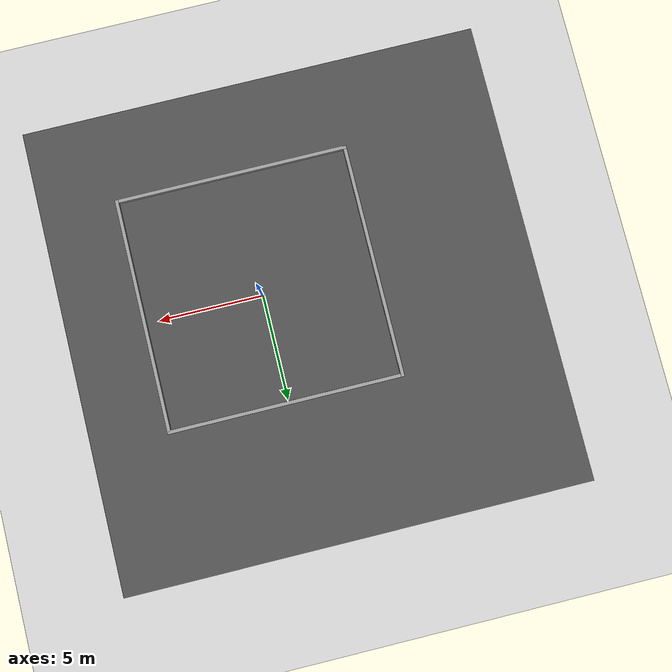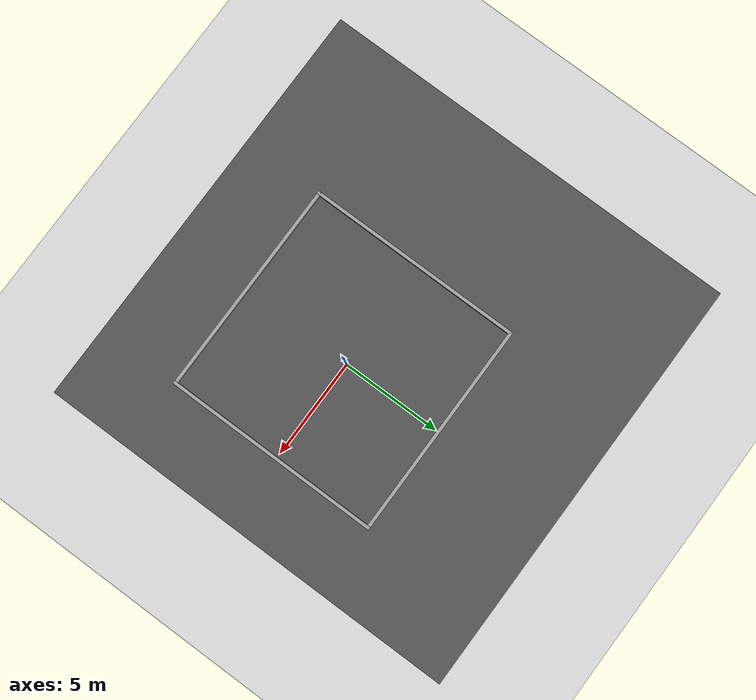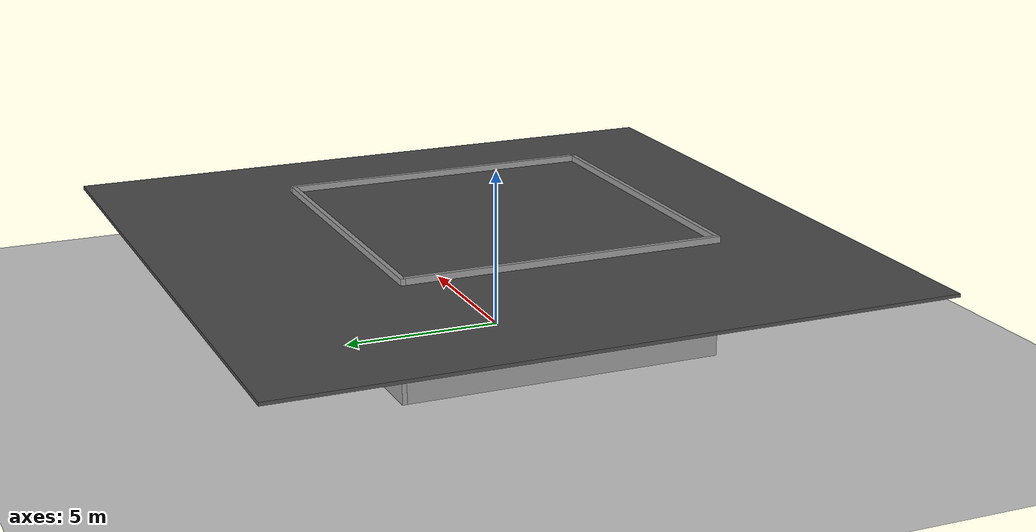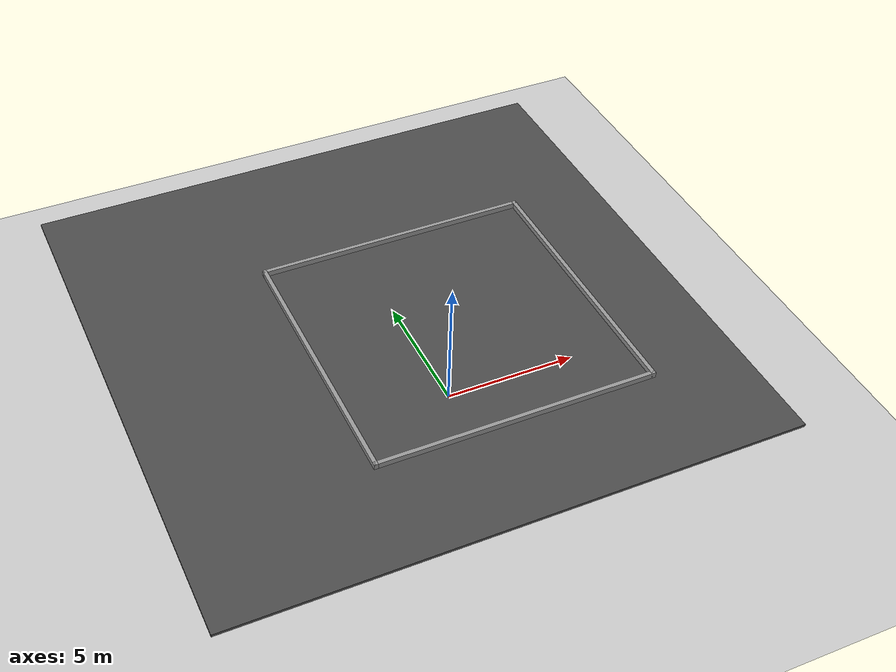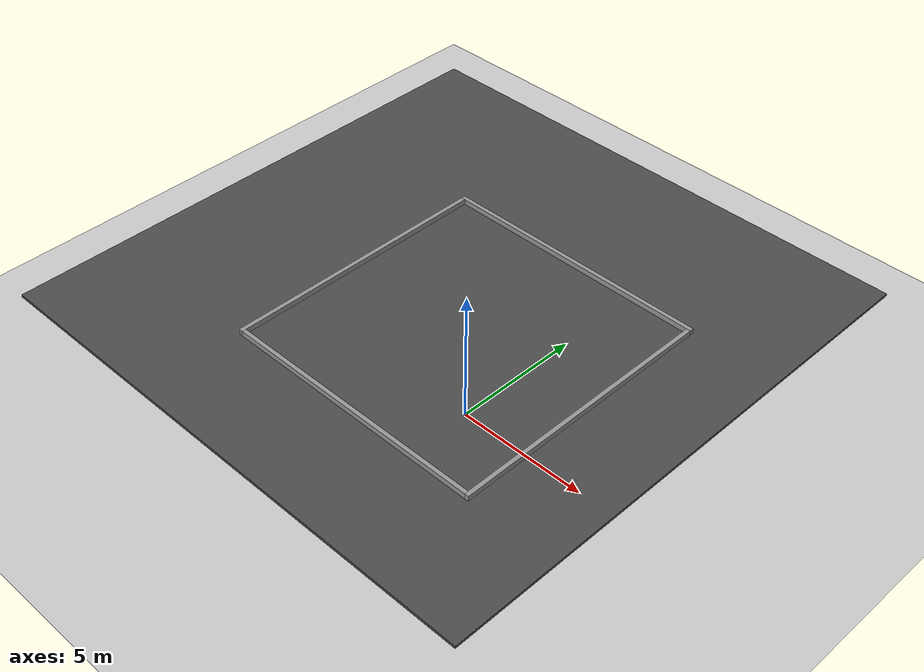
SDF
<sdf version="1.7">
 <world name="default">
  <model name="ground_plane">
   <static>1</static>
   <link name="link">
    <collision name="collision">
     <geometry><plane><normal>0 0 1</normal><size>100 100</size></plane></geometry>
     <surface><friction><ode><mu>100</mu><mu2>50</mu2></ode></friction></surface>
    </collision>
    <visual name="visual">
     <cast_shadows>0</cast_shadows>
     <geometry><plane><normal>0 0 1</normal><size>100 100</size></plane></geometry>
     <material>
      <script><uri>file://media/materials/scripts/gazebo.material</uri><name>Gazebo/Grey</name></script>
     </material>
    </visual>
   </link>
  </model>
  <gravity>0 0 -9.8</gravity>
  <magnetic_field>6e-06 2.3e-05 -4.2e-05</magnetic_field>
  <atmosphere type="adiabatic"/>
  <physics type="ode">
   <max_step_size>0.001</max_step_size>
   <real_time_factor>1</real_time_factor>
   <real_time_update_rate>1000</real_time_update_rate>
  </physics>
  <scene><ambient>0.4 0.4 0.4 1</ambient><background>0.7 0.7 0.7 1</background><shadows>1</shadows></scene>
  <spherical_coordinates>
   <surface_model>EARTH_WGS84</surface_model>
   <latitude_deg>0</latitude_deg>
   <longitude_deg>0</longitude_deg>
   <elevation>0</elevation>
   <heading_deg>0</heading_deg>
  </spherical_coordinates>
  <model name="Indoor_emptyroom">
   <link name="Wall_31">
    <collision name="Wall_31_Collision">
     <geometry><box><size>10.15 0.15 5</size></box></geometry>
     <pose>0 0 1.25 0 -0 0</pose>
    </collision>
    <visual name="Wall_31_Visual">
     <pose>0 0 1.25 0 -0 0</pose>
     <geometry><box><size>10.15 0.15 5</size></box></geometry>
     <material>
      <script><uri>file://media/materials/scripts/gazebo.material</uri><name>Gazebo/Grey</name></script>
      <ambient>1 1 1 1</ambient>
     </material>
     <meta><layer>0</layer></meta>
    </visual>
    <pose>0 -5 0 0 -0 0</pose>
   </link>
   <link name="Wall_32">
    <collision name="Wall_32_Collision">
     <geometry><box><size>10.15 0.15 5</size></box></geometry>
     <pose>0 0 1.25 0 -0 0</pose>
    </collision>
    <visual name="Wall_32_Visual">
     <pose>0 0 1.25 0 -0 0</pose>
     <geometry><box><size>10.15 0.15 5</size></box></geometry>
     <material>
      <script><uri>file://media/materials/scripts/gazebo.material</uri><name>Gazebo/Grey</name></script>
      <ambient>1 1 1 1</ambient>
     </material>
     <meta><layer>0</layer></meta>
    </visual>
    <pose>5 0 0 0 -0 1.5708</pose>
   </link>
   <link name="Wall_33">
    <collision name="Wall_33_Collision">
     <geometry><box><size>10.15 0.15 5</size></box></geometry>
     <pose>0 0 1.25 0 -0 0</pose>
    </collision>
    <visual name="Wall_33_Visual">
     <pose>0 0 1.25 0 -0 0</pose>
     <geometry><box><size>10.15 0.15 5</size></box></geometry>
     <material>
      <script><uri>file://media/materials/scripts/gazebo.material</uri><name>Gazebo/Grey</name></script>
      <ambient>1 1 1 1</ambient>
     </material>
     <meta><layer>0</layer></meta>
    </visual>
    <pose>0 5 0 0 -0 3.14159</pose>
   </link>
   <link name="Wall_34">
    <collision name="Wall_34_Collision">
     <geometry><box><size>10.15 0.15 5</size></box></geometry>
     <pose>0 0 1.25 0 -0 0</pose>
    </collision>
    <visual name="Wall_34_Visual">
     <pose>0 0 1.25 0 -0 0</pose>
     <geometry><box><size>10.15 0.15 5</size></box></geometry>
     <material>
      <script><uri>file://media/materials/scripts/gazebo.material</uri><name>Gazebo/Grey</name></script>
      <ambient>1 1 1 1</ambient>
     </material>
     <meta><layer>0</layer></meta>
    </visual>
    <pose>-5 0 0 0 -0 -1.5708</pose>
   </link>
   <static>1</static>
  </model>
  <model name="small_gate">
   <link name="rod">
    <pose>0 0 0.5 0 -0 0</pose>
    <inertial>
     <mass>1</mass>
     <inertia>
      <ixx>0.166667</ixx>
      <ixy>0</ixy>
      <ixz>0</ixz>
      <iyy>0.166667</iyy>
      <iyz>0</iyz>
      <izz>0.166667</izz>
     </inertia>
    </inertial>
    <visual name="visual">
     <geometry><box><size>0.05 0.05 1</size></box></geometry>
     <material>
      <shader type="vertex"><normal_map>__default__</normal_map></shader>
      <ambient>0.164 0.484 0.978 1</ambient>
      <diffuse>0.164 0.484 0.978 1</diffuse>
      <specular>0.01 0.01 0.01 1</specular>
      <emissive>0 0 0 1</emissive>
     </material>
    </visual>
    <collision name="collision">
     <geometry><box><size>0.05 0.05 1</size></box></geometry>
     <surface>
      <friction>
       <ode><mu>1</mu><mu2>1</mu2><fdir1>0 0 0</fdir1><slip1>0</slip1><slip2>0</slip2></ode>
       <torsional>
        <coefficient>1</coefficient>
        <patch_radius>0</patch_radius>
        <surface_radius>0</surface_radius>
        <use_patch_radius>1</use_patch_radius>
        <ode><slip>0</slip></ode>
       </torsional>
      </friction>
      <bounce><restitution_coefficient>0</restitution_coefficient><threshold>1e+06</threshold></bounce>
      <contact>
       <collide_without_contact>0</collide_without_contact>
       <collide_without_contact_bitmask>1</collide_without_contact_bitmask>
       <collide_bitmask>1</collide_bitmask>
       <ode>
        <soft_cfm>0</soft_cfm>
        <soft_erp>0.2</soft_erp>
        <kp>1e+13</kp>
        <kd>1</kd>
        <max_vel>0.01</max_vel>
        <min_depth>0</min_depth>
       </ode>
       <bullet>
        <split_impulse>1</split_impulse>
        <split_impulse_penetration_threshold>-0.01</split_impulse_penetration_threshold>
        <soft_cfm>0</soft_cfm>
        <soft_erp>0.2</soft_erp>
        <kp>1e+13</kp>
        <kd>1</kd>
       </bullet>
      </contact>
     </surface>
    </collision>
   </link>
   <link name="top_edge">
    <pose>0 0 2 0 -0 0</pose>
    <inertial>
     <mass>1</mass>
     <inertia>
      <ixx>0.166667</ixx>
      <ixy>0</ixy>
      <ixz>0</ixz>
      <iyy>0.166667</iyy>
      <iyz>0</iyz>
      <izz>0.166667</izz>
     </inertia>
    </inertial>
    <visual name="visual">
     <geometry><box><size>1.5 0.05 0.05</size></box></geometry>
     <material>
      <shader type="vertex"><normal_map>__default__</normal_map></shader>
      <ambient>0.164 0.484 0.978 1</ambient>
      <diffuse>0.164 0.484 0.978 1</diffuse>
      <specular>0.01 0.01 0.01 1</specular>
      <emissive>0 0 0 1</emissive>
     </material>
    </visual>
    <collision name="collision">
     <geometry><box><size>1.5 0.05 0.05</size></box></geometry>
     <surface>
      <friction>
       <ode><mu>1</mu><mu2>1</mu2><fdir1>0 0 0</fdir1><slip1>0</slip1><slip2>0</slip2></ode>
       <torsional>
        <coefficient>1</coefficient>
        <patch_radius>0</patch_radius>
        <surface_radius>0</surface_radius>
        <use_patch_radius>1</use_patch_radius>
        <ode><slip>0</slip></ode>
       </torsional>
      </friction>
      <bounce><restitution_coefficient>0</restitution_coefficient><threshold>1e+06</threshold></bounce>
      <contact>
       <collide_without_contact>0</collide_without_contact>
       <collide_without_contact_bitmask>1</collide_without_contact_bitmask>
       <collide_bitmask>1</collide_bitmask>
       <ode>
        <soft_cfm>0</soft_cfm>
        <soft_erp>0.2</soft_erp>
        <kp>1e+13</kp>
        <kd>1</kd>
        <max_vel>0.01</max_vel>
        <min_depth>0</min_depth>
       </ode>
       <bullet>
        <split_impulse>1</split_impulse>
        <split_impulse_penetration_threshold>-0.01</split_impulse_penetration_threshold>
        <soft_cfm>0</soft_cfm>
        <soft_erp>0.2</soft_erp>
        <kp>1e+13</kp>
        <kd>1</kd>
       </bullet>
      </contact>
     </surface>
    </collision>
   </link>
   <link name="bottom_edge">
    <pose>0 0 1 0 -0 0</pose>
    <inertial>
     <mass>1</mass>
     <inertia>
      <ixx>0.166667</ixx>
      <ixy>0</ixy>
      <ixz>0</ixz>
      <iyy>0.166667</iyy>
      <iyz>0</iyz>
      <izz>0.166667</izz>
     </inertia>
    </inertial>
    <visual name="visual">
     <geometry><box><size>1.5 0.05 0.05</size></box></geometry>
     <material>
      <shader type="vertex"><normal_map>__default__</normal_map></shader>
      <ambient>0.164 0.484 0.978 1</ambient>
      <diffuse>0.164 0.484 0.978 1</diffuse>
      <specular>0.01 0.01 0.01 1</specular>
      <emissive>0 0 0 1</emissive>
     </material>
    </visual>
    <collision name="collision">
     <geometry><box><size>1.5 0.05 0.05</size></box></geometry>
     <surface>
      <friction>
       <ode><mu>1</mu><mu2>1</mu2><fdir1>0 0 0</fdir1><slip1>0</slip1><slip2>0</slip2></ode>
       <torsional>
        <coefficient>1</coefficient>
        <patch_radius>0</patch_radius>
        <surface_radius>0</surface_radius>
        <use_patch_radius>1</use_patch_radius>
        <ode><slip>0</slip></ode>
       </torsional>
      </friction>
      <bounce><restitution_coefficient>0</restitution_coefficient><threshold>1e+06</threshold></bounce>
      <contact>
       <collide_without_contact>0</collide_without_contact>
       <collide_without_contact_bitmask>1</collide_without_contact_bitmask>
       <collide_bitmask>1</collide_bitmask>
       <ode>
        <soft_cfm>0</soft_cfm>
        <soft_erp>0.2</soft_erp>
        <kp>1e+13</kp>
        <kd>1</kd>
        <max_vel>0.01</max_vel>
        <min_depth>0</min_depth>
       </ode>
       <bullet>
        <split_impulse>1</split_impulse>
        <split_impulse_penetration_threshold>-0.01</split_impulse_penetration_threshold>
        <soft_cfm>0</soft_cfm>
        <soft_erp>0.2</soft_erp>
        <kp>1e+13</kp>
        <kd>1</kd>
       </bullet>
      </contact>
     </surface>
    </collision>
   </link>
   <link name="left_edge">
    <pose>-0.75 0 1.502 0 -0 0</pose>
    <inertial>
     <mass>1</mass>
     <inertia>
      <ixx>0.166667</ixx>
      <ixy>0</ixy>
      <ixz>0</ixz>
      <iyy>0.166667</iyy>
      <iyz>0</iyz>
      <izz>0.166667</izz>
     </inertia>
    </inertial>
    <visual name="visual">
     <geometry><box><size>0.05 0.05 1.05</size></box></geometry>
     <material>
      <shader type="vertex"><normal_map>__default__</normal_map></shader>
      <ambient>0.164 0.484 0.978 1</ambient>
      <diffuse>0.164 0.484 0.978 1</diffuse>
      <specular>0.01 0.01 0.01 1</specular>
      <emissive>0 0 0 1</emissive>
     </material>
    </visual>
    <collision name="collision">
     <geometry><box><size>0.05 0.05 1.05</size></box></geometry>
     <surface>
      <friction>
       <ode><mu>1</mu><mu2>1</mu2><fdir1>0 0 0</fdir1><slip1>0</slip1><slip2>0</slip2></ode>
       <torsional>
        <coefficient>1</coefficient>
        <patch_radius>0</patch_radius>
        <surface_radius>0</surface_radius>
        <use_patch_radius>1</use_patch_radius>
        <ode><slip>0</slip></ode>
       </torsional>
      </friction>
      <bounce><restitution_coefficient>0</restitution_coefficient><threshold>1e+06</threshold></bounce>
      <contact>
       <collide_without_contact>0</collide_without_contact>
       <collide_without_contact_bitmask>1</collide_without_contact_bitmask>
       <collide_bitmask>1</collide_bitmask>
       <ode>
        <soft_cfm>0</soft_cfm>
        <soft_erp>0.2</soft_erp>
        <kp>1e+13</kp>
        <kd>1</kd>
        <max_vel>0.01</max_vel>
        <min_depth>0</min_depth>
       </ode>
       <bullet>
        <split_impulse>1</split_impulse>
        <split_impulse_penetration_threshold>-0.01</split_impulse_penetration_threshold>
        <soft_cfm>0</soft_cfm>
        <soft_erp>0.2</soft_erp>
        <kp>1e+13</kp>
        <kd>1</kd>
       </bullet>
      </contact>
     </surface>
    </collision>
   </link>
   <link name="right_edge">
    <pose>0.75 0 1.502 0 -0 0</pose>
    <inertial>
     <mass>1</mass>
     <inertia>
      <ixx>0.166667</ixx>
      <ixy>0</ixy>
      <ixz>0</ixz>
      <iyy>0.166667</iyy>
      <iyz>0</iyz>
      <izz>0.166667</izz>
     </inertia>
    </inertial>
    <visual name="visual">
     <geometry><box><size>0.05 0.05 1.05</size></box></geometry>
     <material>
      <shader type="vertex"><normal_map>__default__</normal_map></shader>
      <ambient>0.164 0.484 0.978 1</ambient>
      <diffuse>0.164 0.484 0.978 1</diffuse>
      <specular>0.01 0.01 0.01 1</specular>
      <emissive>0 0 0 1</emissive>
     </material>
    </visual>
    <collision name="collision">
     <geometry><box><size>0.05 0.05 1.05</size></box></geometry>
     <surface>
      <friction>
       <ode><mu>1</mu><mu2>1</mu2><fdir1>0 0 0</fdir1><slip1>0</slip1><slip2>0</slip2></ode>
       <torsional>
        <coefficient>1</coefficient>
        <patch_radius>0</patch_radius>
        <surface_radius>0</surface_radius>
        <use_patch_radius>1</use_patch_radius>
        <ode><slip>0</slip></ode>
       </torsional>
      </friction>
      <bounce><restitution_coefficient>0</restitution_coefficient><threshold>1e+06</threshold></bounce>
      <contact>
       <collide_without_contact>0</collide_without_contact>
       <collide_without_contact_bitmask>1</collide_without_contact_bitmask>
       <collide_bitmask>1</collide_bitmask>
       <ode>
        <soft_cfm>0</soft_cfm>
        <soft_erp>0.2</soft_erp>
        <kp>1e+13</kp>
        <kd>1</kd>
        <max_vel>0.01</max_vel>
        <min_depth>0</min_depth>
       </ode>
       <bullet>
        <split_impulse>1</split_impulse>
        <split_impulse_penetration_threshold>-0.01</split_impulse_penetration_threshold>
        <soft_cfm>0</soft_cfm>
        <soft_erp>0.2</soft_erp>
        <kp>1e+13</kp>
        <kd>1</kd>
       </bullet>
      </contact>
     </surface>
    </collision>
   </link>
   <static>1</static>
   <pose>-3.25 -2 0 0 -0 0</pose>
  </model>
  <model name="small_gate_0">
   <link name="rod">
    <pose>0 0 0.5 0 -0 0</pose>
    <inertial>
     <mass>1</mass>
     <inertia>
      <ixx>0.166667</ixx>
      <ixy>0</ixy>
      <ixz>0</ixz>
      <iyy>0.166667</iyy>
      <iyz>0</iyz>
      <izz>0.166667</izz>
     </inertia>
    </inertial>
    <visual name="visual">
     <geometry><box><size>0.05 0.05 1</size></box></geometry>
     <material>
      <shader type="vertex"><normal_map>__default__</normal_map></shader>
      <ambient>0.164 0.484 0.978 1</ambient>
      <diffuse>0.164 0.484 0.978 1</diffuse>
      <specular>0.01 0.01 0.01 1</specular>
      <emissive>0 0 0 1</emissive>
     </material>
    </visual>
    <collision name="collision">
     <geometry><box><size>0.05 0.05 1</size></box></geometry>
     <surface>
      <friction>
       <ode><mu>1</mu><mu2>1</mu2><fdir1>0 0 0</fdir1><slip1>0</slip1><slip2>0</slip2></ode>
       <torsional>
        <coefficient>1</coefficient>
        <patch_radius>0</patch_radius>
        <surface_radius>0</surface_radius>
        <use_patch_radius>1</use_patch_radius>
        <ode><slip>0</slip></ode>
       </torsional>
      </friction>
      <bounce><restitution_coefficient>0</restitution_coefficient><threshold>1e+06</threshold></bounce>
      <contact>
       <collide_without_contact>0</collide_without_contact>
       <collide_without_contact_bitmask>1</collide_without_contact_bitmask>
       <collide_bitmask>1</collide_bitmask>
       <ode>
        <soft_cfm>0</soft_cfm>
        <soft_erp>0.2</soft_erp>
        <kp>1e+13</kp>
        <kd>1</kd>
        <max_vel>0.01</max_vel>
        <min_depth>0</min_depth>
       </ode>
       <bullet>
        <split_impulse>1</split_impulse>
        <split_impulse_penetration_threshold>-0.01</split_impulse_penetration_threshold>
        <soft_cfm>0</soft_cfm>
        <soft_erp>0.2</soft_erp>
        <kp>1e+13</kp>
        <kd>1</kd>
       </bullet>
      </contact>
     </surface>
    </collision>
   </link>
   <link name="top_edge">
    <pose>0 0 2 0 -0 0</pose>
    <inertial>
     <mass>1</mass>
     <inertia>
      <ixx>0.166667</ixx>
      <ixy>0</ixy>
      <ixz>0</ixz>
      <iyy>0.166667</iyy>
      <iyz>0</iyz>
      <izz>0.166667</izz>
     </inertia>
    </inertial>
    <visual name="visual">
     <geometry><box><size>1.5 0.05 0.05</size></box></geometry>
     <material>
      <shader type="vertex"><normal_map>__default__</normal_map></shader>
      <ambient>0.164 0.484 0.978 1</ambient>
      <diffuse>0.164 0.484 0.978 1</diffuse>
      <specular>0.01 0.01 0.01 1</specular>
      <emissive>0 0 0 1</emissive>
     </material>
    </visual>
    <collision name="collision">
     <geometry><box><size>1.5 0.05 0.05</size></box></geometry>
     <surface>
      <friction>
       <ode><mu>1</mu><mu2>1</mu2><fdir1>0 0 0</fdir1><slip1>0</slip1><slip2>0</slip2></ode>
       <torsional>
        <coefficient>1</coefficient>
        <patch_radius>0</patch_radius>
        <surface_radius>0</surface_radius>
        <use_patch_radius>1</use_patch_radius>
        <ode><slip>0</slip></ode>
       </torsional>
      </friction>
      <bounce><restitution_coefficient>0</restitution_coefficient><threshold>1e+06</threshold></bounce>
      <contact>
       <collide_without_contact>0</collide_without_contact>
       <collide_without_contact_bitmask>1</collide_without_contact_bitmask>
       <collide_bitmask>1</collide_bitmask>
       <ode>
        <soft_cfm>0</soft_cfm>
        <soft_erp>0.2</soft_erp>
        <kp>1e+13</kp>
        <kd>1</kd>
        <max_vel>0.01</max_vel>
        <min_depth>0</min_depth>
       </ode>
       <bullet>
        <split_impulse>1</split_impulse>
        <split_impulse_penetration_threshold>-0.01</split_impulse_penetration_threshold>
        <soft_cfm>0</soft_cfm>
        <soft_erp>0.2</soft_erp>
        <kp>1e+13</kp>
        <kd>1</kd>
       </bullet>
      </contact>
     </surface>
    </collision>
   </link>
   <link name="bottom_edge">
    <pose>0 0 1 0 -0 0</pose>
    <inertial>
     <mass>1</mass>
     <inertia>
      <ixx>0.166667</ixx>
      <ixy>0</ixy>
      <ixz>0</ixz>
      <iyy>0.166667</iyy>
      <iyz>0</iyz>
      <izz>0.166667</izz>
     </inertia>
    </inertial>
    <visual name="visual">
     <geometry><box><size>1.5 0.05 0.05</size></box></geometry>
     <material>
      <shader type="vertex"><normal_map>__default__</normal_map></shader>
      <ambient>0.164 0.484 0.978 1</ambient>
      <diffuse>0.164 0.484 0.978 1</diffuse>
      <specular>0.01 0.01 0.01 1</specular>
      <emissive>0 0 0 1</emissive>
     </material>
    </visual>
    <collision name="collision">
     <geometry><box><size>1.5 0.05 0.05</size></box></geometry>
     <surface>
      <friction>
       <ode><mu>1</mu><mu2>1</mu2><fdir1>0 0 0</fdir1><slip1>0</slip1><slip2>0</slip2></ode>
       <torsional>
        <coefficient>1</coefficient>
        <patch_radius>0</patch_radius>
        <surface_radius>0</surface_radius>
        <use_patch_radius>1</use_patch_radius>
        <ode><slip>0</slip></ode>
       </torsional>
      </friction>
      <bounce><restitution_coefficient>0</restitution_coefficient><threshold>1e+06</threshold></bounce>
      <contact>
       <collide_without_contact>0</collide_without_contact>
       <collide_without_contact_bitmask>1</collide_without_contact_bitmask>
       <collide_bitmask>1</collide_bitmask>
       <ode>
        <soft_cfm>0</soft_cfm>
        <soft_erp>0.2</soft_erp>
        <kp>1e+13</kp>
        <kd>1</kd>
        <max_vel>0.01</max_vel>
        <min_depth>0</min_depth>
       </ode>
       <bullet>
        <split_impulse>1</split_impulse>
        <split_impulse_penetration_threshold>-0.01</split_impulse_penetration_threshold>
        <soft_cfm>0</soft_cfm>
        <soft_erp>0.2</soft_erp>
        <kp>1e+13</kp>
        <kd>1</kd>
       </bullet>
      </contact>
     </surface>
    </collision>
   </link>
   <link name="left_edge">
    <pose>-0.75 0 1.502 0 -0 0</pose>
    <inertial>
     <mass>1</mass>
     <inertia>
      <ixx>0.166667</ixx>
      <ixy>0</ixy>
      <ixz>0</ixz>
      <iyy>0.166667</iyy>
      <iyz>0</iyz>
      <izz>0.166667</izz>
     </inertia>
    </inertial>
    <visual name="visual">
     <geometry><box><size>0.05 0.05 1.05</size></box></geometry>
     <material>
      <shader type="vertex"><normal_map>__default__</normal_map></shader>
      <ambient>0.164 0.484 0.978 1</ambient>
      <diffuse>0.164 0.484 0.978 1</diffuse>
      <specular>0.01 0.01 0.01 1</specular>
      <emissive>0 0 0 1</emissive>
     </material>
    </visual>
    <collision name="collision">
     <geometry><box><size>0.05 0.05 1.05</size></box></geometry>
     <surface>
      <friction>
       <ode><mu>1</mu><mu2>1</mu2><fdir1>0 0 0</fdir1><slip1>0</slip1><slip2>0</slip2></ode>
       <torsional>
        <coefficient>1</coefficient>
        <patch_radius>0</patch_radius>
        <surface_radius>0</surface_radius>
        <use_patch_radius>1</use_patch_radius>
        <ode><slip>0</slip></ode>
       </torsional>
      </friction>
      <bounce><restitution_coefficient>0</restitution_coefficient><threshold>1e+06</threshold></bounce>
      <contact>
       <collide_without_contact>0</collide_without_contact>
       <collide_without_contact_bitmask>1</collide_without_contact_bitmask>
       <collide_bitmask>1</collide_bitmask>
       <ode>
        <soft_cfm>0</soft_cfm>
        <soft_erp>0.2</soft_erp>
        <kp>1e+13</kp>
        <kd>1</kd>
        <max_vel>0.01</max_vel>
        <min_depth>0</min_depth>
       </ode>
       <bullet>
        <split_impulse>1</split_impulse>
        <split_impulse_penetration_threshold>-0.01</split_impulse_penetration_threshold>
        <soft_cfm>0</soft_cfm>
        <soft_erp>0.2</soft_erp>
        <kp>1e+13</kp>
        <kd>1</kd>
       </bullet>
      </contact>
     </surface>
    </collision>
   </link>
   <link name="right_edge">
    <pose>0.75 0 1.502 0 -0 0</pose>
    <inertial>
     <mass>1</mass>
     <inertia>
      <ixx>0.166667</ixx>
      <ixy>0</ixy>
      <ixz>0</ixz>
      <iyy>0.166667</iyy>
      <iyz>0</iyz>
      <izz>0.166667</izz>
     </inertia>
    </inertial>
    <visual name="visual">
     <geometry><box><size>0.05 0.05 1.05</size></box></geometry>
     <material>
      <shader type="vertex"><normal_map>__default__</normal_map></shader>
      <ambient>0.164 0.484 0.978 1</ambient>
      <diffuse>0.164 0.484 0.978 1</diffuse>
      <specular>0.01 0.01 0.01 1</specular>
      <emissive>0 0 0 1</emissive>
     </material>
    </visual>
    <collision name="collision">
     <geometry><box><size>0.05 0.05 1.05</size></box></geometry>
     <surface>
      <friction>
       <ode><mu>1</mu><mu2>1</mu2><fdir1>0 0 0</fdir1><slip1>0</slip1><slip2>0</slip2></ode>
       <torsional>
        <coefficient>1</coefficient>
        <patch_radius>0</patch_radius>
        <surface_radius>0</surface_radius>
        <use_patch_radius>1</use_patch_radius>
        <ode><slip>0</slip></ode>
       </torsional>
      </friction>
      <bounce><restitution_coefficient>0</restitution_coefficient><threshold>1e+06</threshold></bounce>
      <contact>
       <collide_without_contact>0</collide_without_contact>
       <collide_without_contact_bitmask>1</collide_without_contact_bitmask>
       <collide_bitmask>1</collide_bitmask>
       <ode>
        <soft_cfm>0</soft_cfm>
        <soft_erp>0.2</soft_erp>
        <kp>1e+13</kp>
        <kd>1</kd>
        <max_vel>0.01</max_vel>
        <min_depth>0</min_depth>
       </ode>
       <bullet>
        <split_impulse>1</split_impulse>
        <split_impulse_penetration_threshold>-0.01</split_impulse_penetration_threshold>
        <soft_cfm>0</soft_cfm>
        <soft_erp>0.2</soft_erp>
        <kp>1e+13</kp>
        <kd>1</kd>
       </bullet>
      </contact>
     </surface>
    </collision>
   </link>
   <static>1</static>
   <pose>-3.25 -1.5 0 0 -0 0</pose>
  </model>
  <model name="small_gate_1">
   <link name="rod">
    <pose>0 0 0.5 0 -0 0</pose>
    <inertial>
     <mass>1</mass>
     <inertia>
      <ixx>0.166667</ixx>
      <ixy>0</ixy>
      <ixz>0</ixz>
      <iyy>0.166667</iyy>
      <iyz>0</iyz>
      <izz>0.166667</izz>
     </inertia>
    </inertial>
    <visual name="visual">
     <geometry><box><size>0.05 0.05 1</size></box></geometry>
     <material>
      <shader type="vertex"><normal_map>__default__</normal_map></shader>
      <ambient>0.164 0.484 0.978 1</ambient>
      <diffuse>0.164 0.484 0.978 1</diffuse>
      <specular>0.01 0.01 0.01 1</specular>
      <emissive>0 0 0 1</emissive>
     </material>
    </visual>
    <collision name="collision">
     <geometry><box><size>0.05 0.05 1</size></box></geometry>
     <surface>
      <friction>
       <ode><mu>1</mu><mu2>1</mu2><fdir1>0 0 0</fdir1><slip1>0</slip1><slip2>0</slip2></ode>
       <torsional>
        <coefficient>1</coefficient>
        <patch_radius>0</patch_radius>
        <surface_radius>0</surface_radius>
        <use_patch_radius>1</use_patch_radius>
        <ode><slip>0</slip></ode>
       </torsional>
      </friction>
      <bounce><restitution_coefficient>0</restitution_coefficient><threshold>1e+06</threshold></bounce>
      <contact>
       <collide_without_contact>0</collide_without_contact>
       <collide_without_contact_bitmask>1</collide_without_contact_bitmask>
       <collide_bitmask>1</collide_bitmask>
       <ode>
        <soft_cfm>0</soft_cfm>
        <soft_erp>0.2</soft_erp>
        <kp>1e+13</kp>
        <kd>1</kd>
        <max_vel>0.01</max_vel>
        <min_depth>0</min_depth>
       </ode>
       <bullet>
        <split_impulse>1</split_impulse>
        <split_impulse_penetration_threshold>-0.01</split_impulse_penetration_threshold>
        <soft_cfm>0</soft_cfm>
        <soft_erp>0.2</soft_erp>
        <kp>1e+13</kp>
        <kd>1</kd>
       </bullet>
      </contact>
     </surface>
    </collision>
   </link>
   <link name="top_edge">
    <pose>0 0 2 0 -0 0</pose>
    <inertial>
     <mass>1</mass>
     <inertia>
      <ixx>0.166667</ixx>
      <ixy>0</ixy>
      <ixz>0</ixz>
      <iyy>0.166667</iyy>
      <iyz>0</iyz>
      <izz>0.166667</izz>
     </inertia>
    </inertial>
    <visual name="visual">
     <geometry><box><size>1.5 0.05 0.05</size></box></geometry>
     <material>
      <shader type="vertex"><normal_map>__default__</normal_map></shader>
      <ambient>0.164 0.484 0.978 1</ambient>
      <diffuse>0.164 0.484 0.978 1</diffuse>
      <specular>0.01 0.01 0.01 1</specular>
      <emissive>0 0 0 1</emissive>
     </material>
    </visual>
    <collision name="collision">
     <geometry><box><size>1.5 0.05 0.05</size></box></geometry>
     <surface>
      <friction>
       <ode><mu>1</mu><mu2>1</mu2><fdir1>0 0 0</fdir1><slip1>0</slip1><slip2>0</slip2></ode>
       <torsional>
        <coefficient>1</coefficient>
        <patch_radius>0</patch_radius>
        <surface_radius>0</surface_radius>
        <use_patch_radius>1</use_patch_radius>
        <ode><slip>0</slip></ode>
       </torsional>
      </friction>
      <bounce><restitution_coefficient>0</restitution_coefficient><threshold>1e+06</threshold></bounce>
      <contact>
       <collide_without_contact>0</collide_without_contact>
       <collide_without_contact_bitmask>1</collide_without_contact_bitmask>
       <collide_bitmask>1</collide_bitmask>
       <ode>
        <soft_cfm>0</soft_cfm>
        <soft_erp>0.2</soft_erp>
        <kp>1e+13</kp>
        <kd>1</kd>
        <max_vel>0.01</max_vel>
        <min_depth>0</min_depth>
       </ode>
       <bullet>
        <split_impulse>1</split_impulse>
        <split_impulse_penetration_threshold>-0.01</split_impulse_penetration_threshold>
        <soft_cfm>0</soft_cfm>
        <soft_erp>0.2</soft_erp>
        <kp>1e+13</kp>
        <kd>1</kd>
       </bullet>
      </contact>
     </surface>
    </collision>
   </link>
   <link name="bottom_edge">
    <pose>0 0 1 0 -0 0</pose>
    <inertial>
     <mass>1</mass>
     <inertia>
      <ixx>0.166667</ixx>
      <ixy>0</ixy>
      <ixz>0</ixz>
      <iyy>0.166667</iyy>
      <iyz>0</iyz>
      <izz>0.166667</izz>
     </inertia>
    </inertial>
    <visual name="visual">
     <geometry><box><size>1.5 0.05 0.05</size></box></geometry>
     <material>
      <shader type="vertex"><normal_map>__default__</normal_map></shader>
      <ambient>0.164 0.484 0.978 1</ambient>
      <diffuse>0.164 0.484 0.978 1</diffuse>
      <specular>0.01 0.01 0.01 1</specular>
      <emissive>0 0 0 1</emissive>
     </material>
    </visual>
    <collision name="collision">
     <geometry><box><size>1.5 0.05 0.05</size></box></geometry>
     <surface>
      <friction>
       <ode><mu>1</mu><mu2>1</mu2><fdir1>0 0 0</fdir1><slip1>0</slip1><slip2>0</slip2></ode>
       <torsional>
        <coefficient>1</coefficient>
        <patch_radius>0</patch_radius>
        <surface_radius>0</surface_radius>
        <use_patch_radius>1</use_patch_radius>
        <ode><slip>0</slip></ode>
       </torsional>
      </friction>
      <bounce><restitution_coefficient>0</restitution_coefficient><threshold>1e+06</threshold></bounce>
      <contact>
       <collide_without_contact>0</collide_without_contact>
       <collide_without_contact_bitmask>1</collide_without_contact_bitmask>
       <collide_bitmask>1</collide_bitmask>
       <ode>
        <soft_cfm>0</soft_cfm>
        <soft_erp>0.2</soft_erp>
        <kp>1e+13</kp>
        <kd>1</kd>
        <max_vel>0.01</max_vel>
        <min_depth>0</min_depth>
       </ode>
       <bullet>
        <split_impulse>1</split_impulse>
        <split_impulse_penetration_threshold>-0.01</split_impulse_penetration_threshold>
        <soft_cfm>0</soft_cfm>
        <soft_erp>0.2</soft_erp>
        <kp>1e+13</kp>
        <kd>1</kd>
       </bullet>
      </contact>
     </surface>
    </collision>
   </link>
   <link name="left_edge">
    <pose>-0.75 0 1.502 0 -0 0</pose>
    <inertial>
     <mass>1</mass>
     <inertia>
      <ixx>0.166667</ixx>
      <ixy>0</ixy>
      <ixz>0</ixz>
      <iyy>0.166667</iyy>
      <iyz>0</iyz>
      <izz>0.166667</izz>
     </inertia>
    </inertial>
    <visual name="visual">
     <geometry><box><size>0.05 0.05 1.05</size></box></geometry>
     <material>
      <shader type="vertex"><normal_map>__default__</normal_map></shader>
      <ambient>0.164 0.484 0.978 1</ambient>
      <diffuse>0.164 0.484 0.978 1</diffuse>
      <specular>0.01 0.01 0.01 1</specular>
      <emissive>0 0 0 1</emissive>
     </material>
    </visual>
    <collision name="collision">
     <geometry><box><size>0.05 0.05 1.05</size></box></geometry>
     <surface>
      <friction>
       <ode><mu>1</mu><mu2>1</mu2><fdir1>0 0 0</fdir1><slip1>0</slip1><slip2>0</slip2></ode>
       <torsional>
        <coefficient>1</coefficient>
        <patch_radius>0</patch_radius>
        <surface_radius>0</surface_radius>
        <use_patch_radius>1</use_patch_radius>
        <ode><slip>0</slip></ode>
       </torsional>
      </friction>
      <bounce><restitution_coefficient>0</restitution_coefficient><threshold>1e+06</threshold></bounce>
      <contact>
       <collide_without_contact>0</collide_without_contact>
       <collide_without_contact_bitmask>1</collide_without_contact_bitmask>
       <collide_bitmask>1</collide_bitmask>
       <ode>
        <soft_cfm>0</soft_cfm>
        <soft_erp>0.2</soft_erp>
        <kp>1e+13</kp>
        <kd>1</kd>
        <max_vel>0.01</max_vel>
        <min_depth>0</min_depth>
       </ode>
       <bullet>
        <split_impulse>1</split_impulse>
        <split_impulse_penetration_threshold>-0.01</split_impulse_penetration_threshold>
        <soft_cfm>0</soft_cfm>
        <soft_erp>0.2</soft_erp>
        <kp>1e+13</kp>
        <kd>1</kd>
       </bullet>
      </contact>
     </surface>
    </collision>
   </link>
   <link name="right_edge">
    <pose>0.75 0 1.502 0 -0 0</pose>
    <inertial>
     <mass>1</mass>
     <inertia>
      <ixx>0.166667</ixx>
      <ixy>0</ixy>
      <ixz>0</ixz>
      <iyy>0.166667</iyy>
      <iyz>0</iyz>
      <izz>0.166667</izz>
     </inertia>
    </inertial>
    <visual name="visual">
     <geometry><box><size>0.05 0.05 1.05</size></box></geometry>
     <material>
      <shader type="vertex"><normal_map>__default__</normal_map></shader>
      <ambient>0.164 0.484 0.978 1</ambient>
      <diffuse>0.164 0.484 0.978 1</diffuse>
      <specular>0.01 0.01 0.01 1</specular>
      <emissive>0 0 0 1</emissive>
     </material>
    </visual>
    <collision name="collision">
     <geometry><box><size>0.05 0.05 1.05</size></box></geometry>
     <surface>
      <friction>
       <ode><mu>1</mu><mu2>1</mu2><fdir1>0 0 0</fdir1><slip1>0</slip1><slip2>0</slip2></ode>
       <torsional>
        <coefficient>1</coefficient>
        <patch_radius>0</patch_radius>
        <surface_radius>0</surface_radius>
        <use_patch_radius>1</use_patch_radius>
        <ode><slip>0</slip></ode>
       </torsional>
      </friction>
      <bounce><restitution_coefficient>0</restitution_coefficient><threshold>1e+06</threshold></bounce>
      <contact>
       <collide_without_contact>0</collide_without_contact>
       <collide_without_contact_bitmask>1</collide_without_contact_bitmask>
       <collide_bitmask>1</collide_bitmask>
       <ode>
        <soft_cfm>0</soft_cfm>
        <soft_erp>0.2</soft_erp>
        <kp>1e+13</kp>
        <kd>1</kd>
        <max_vel>0.01</max_vel>
        <min_depth>0</min_depth>
       </ode>
       <bullet>
        <split_impulse>1</split_impulse>
        <split_impulse_penetration_threshold>-0.01</split_impulse_penetration_threshold>
        <soft_cfm>0</soft_cfm>
        <soft_erp>0.2</soft_erp>
        <kp>1e+13</kp>
        <kd>1</kd>
       </bullet>
      </contact>
     </surface>
    </collision>
   </link>
   <static>1</static>
   <pose>-3.25 -1 0 0 -0 0</pose>
  </model>
  <model name="small_gate_2">
   <link name="rod">
    <pose>0 0 0.5 0 -0 0</pose>
    <inertial>
     <mass>1</mass>
     <inertia>
      <ixx>0.166667</ixx>
      <ixy>0</ixy>
      <ixz>0</ixz>
      <iyy>0.166667</iyy>
      <iyz>0</iyz>
      <izz>0.166667</izz>
     </inertia>
    </inertial>
    <visual name="visual">
     <geometry><box><size>0.05 0.05 1</size></box></geometry>
     <material>
      <shader type="vertex"><normal_map>__default__</normal_map></shader>
      <ambient>0.164 0.484 0.978 1</ambient>
      <diffuse>0.164 0.484 0.978 1</diffuse>
      <specular>0.01 0.01 0.01 1</specular>
      <emissive>0 0 0 1</emissive>
     </material>
    </visual>
    <collision name="collision">
     <geometry><box><size>0.05 0.05 1</size></box></geometry>
     <surface>
      <friction>
       <ode><mu>1</mu><mu2>1</mu2><fdir1>0 0 0</fdir1><slip1>0</slip1><slip2>0</slip2></ode>
       <torsional>
        <coefficient>1</coefficient>
        <patch_radius>0</patch_radius>
        <surface_radius>0</surface_radius>
        <use_patch_radius>1</use_patch_radius>
        <ode><slip>0</slip></ode>
       </torsional>
      </friction>
      <bounce><restitution_coefficient>0</restitution_coefficient><threshold>1e+06</threshold></bounce>
      <contact>
       <collide_without_contact>0</collide_without_contact>
       <collide_without_contact_bitmask>1</collide_without_contact_bitmask>
       <collide_bitmask>1</collide_bitmask>
       <ode>
        <soft_cfm>0</soft_cfm>
        <soft_erp>0.2</soft_erp>
        <kp>1e+13</kp>
        <kd>1</kd>
        <max_vel>0.01</max_vel>
        <min_depth>0</min_depth>
       </ode>
       <bullet>
        <split_impulse>1</split_impulse>
        <split_impulse_penetration_threshold>-0.01</split_impulse_penetration_threshold>
        <soft_cfm>0</soft_cfm>
        <soft_erp>0.2</soft_erp>
        <kp>1e+13</kp>
        <kd>1</kd>
       </bullet>
      </contact>
     </surface>
    </collision>
   </link>
   <link name="top_edge">
    <pose>0 0 2 0 -0 0</pose>
    <inertial>
     <mass>1</mass>
     <inertia>
      <ixx>0.166667</ixx>
      <ixy>0</ixy>
      <ixz>0</ixz>
      <iyy>0.166667</iyy>
      <iyz>0</iyz>
      <izz>0.166667</izz>
     </inertia>
    </inertial>
    <visual name="visual">
     <geometry><box><size>1.5 0.05 0.05</size></box></geometry>
     <material>
      <shader type="vertex"><normal_map>__default__</normal_map></shader>
      <ambient>0.164 0.484 0.978 1</ambient>
      <diffuse>0.164 0.484 0.978 1</diffuse>
      <specular>0.01 0.01 0.01 1</specular>
      <emissive>0 0 0 1</emissive>
     </material>
    </visual>
    <collision name="collision">
     <geometry><box><size>1.5 0.05 0.05</size></box></geometry>
     <surface>
      <friction>
       <ode><mu>1</mu><mu2>1</mu2><fdir1>0 0 0</fdir1><slip1>0</slip1><slip2>0</slip2></ode>
       <torsional>
        <coefficient>1</coefficient>
        <patch_radius>0</patch_radius>
        <surface_radius>0</surface_radius>
        <use_patch_radius>1</use_patch_radius>
        <ode><slip>0</slip></ode>
       </torsional>
      </friction>
      <bounce><restitution_coefficient>0</restitution_coefficient><threshold>1e+06</threshold></bounce>
      <contact>
       <collide_without_contact>0</collide_without_contact>
       <collide_without_contact_bitmask>1</collide_without_contact_bitmask>
       <collide_bitmask>1</collide_bitmask>
       <ode>
        <soft_cfm>0</soft_cfm>
        <soft_erp>0.2</soft_erp>
        <kp>1e+13</kp>
        <kd>1</kd>
        <max_vel>0.01</max_vel>
        <min_depth>0</min_depth>
       </ode>
       <bullet>
        <split_impulse>1</split_impulse>
        <split_impulse_penetration_threshold>-0.01</split_impulse_penetration_threshold>
        <soft_cfm>0</soft_cfm>
        <soft_erp>0.2</soft_erp>
        <kp>1e+13</kp>
        <kd>1</kd>
       </bullet>
      </contact>
     </surface>
    </collision>
   </link>
   <link name="bottom_edge">
    <pose>0 0 1 0 -0 0</pose>
    <inertial>
     <mass>1</mass>
     <inertia>
      <ixx>0.166667</ixx>
      <ixy>0</ixy>
      <ixz>0</ixz>
      <iyy>0.166667</iyy>
      <iyz>0</iyz>
      <izz>0.166667</izz>
     </inertia>
    </inertial>
    <visual name="visual">
     <geometry><box><size>1.5 0.05 0.05</size></box></geometry>
     <material>
      <shader type="vertex"><normal_map>__default__</normal_map></shader>
      <ambient>0.164 0.484 0.978 1</ambient>
      <diffuse>0.164 0.484 0.978 1</diffuse>
      <specular>0.01 0.01 0.01 1</specular>
      <emissive>0 0 0 1</emissive>
     </material>
    </visual>
    <collision name="collision">
     <geometry><box><size>1.5 0.05 0.05</size></box></geometry>
     <surface>
      <friction>
       <ode><mu>1</mu><mu2>1</mu2><fdir1>0 0 0</fdir1><slip1>0</slip1><slip2>0</slip2></ode>
       <torsional>
        <coefficient>1</coefficient>
        <patch_radius>0</patch_radius>
        <surface_radius>0</surface_radius>
        <use_patch_radius>1</use_patch_radius>
        <ode><slip>0</slip></ode>
       </torsional>
      </friction>
      <bounce><restitution_coefficient>0</restitution_coefficient><threshold>1e+06</threshold></bounce>
      <contact>
       <collide_without_contact>0</collide_without_contact>
       <collide_without_contact_bitmask>1</collide_without_contact_bitmask>
       <collide_bitmask>1</collide_bitmask>
       <ode>
        <soft_cfm>0</soft_cfm>
        <soft_erp>0.2</soft_erp>
        <kp>1e+13</kp>
        <kd>1</kd>
        <max_vel>0.01</max_vel>
        <min_depth>0</min_depth>
       </ode>
       <bullet>
        <split_impulse>1</split_impulse>
        <split_impulse_penetration_threshold>-0.01</split_impulse_penetration_threshold>
        <soft_cfm>0</soft_cfm>
        <soft_erp>0.2</soft_erp>
        <kp>1e+13</kp>
        <kd>1</kd>
       </bullet>
      </contact>
     </surface>
    </collision>
   </link>
   <link name="left_edge">
    <pose>-0.75 0 1.502 0 -0 0</pose>
    <inertial>
     <mass>1</mass>
     <inertia>
      <ixx>0.166667</ixx>
      <ixy>0</ixy>
      <ixz>0</ixz>
      <iyy>0.166667</iyy>
      <iyz>0</iyz>
      <izz>0.166667</izz>
     </inertia>
    </inertial>
    <visual name="visual">
     <geometry><box><size>0.05 0.05 1.05</size></box></geometry>
     <material>
      <shader type="vertex"><normal_map>__default__</normal_map></shader>
      <ambient>0.164 0.484 0.978 1</ambient>
      <diffuse>0.164 0.484 0.978 1</diffuse>
      <specular>0.01 0.01 0.01 1</specular>
      <emissive>0 0 0 1</emissive>
     </material>
    </visual>
    <collision name="collision">
     <geometry><box><size>0.05 0.05 1.05</size></box></geometry>
     <surface>
      <friction>
       <ode><mu>1</mu><mu2>1</mu2><fdir1>0 0 0</fdir1><slip1>0</slip1><slip2>0</slip2></ode>
       <torsional>
        <coefficient>1</coefficient>
        <patch_radius>0</patch_radius>
        <surface_radius>0</surface_radius>
        <use_patch_radius>1</use_patch_radius>
        <ode><slip>0</slip></ode>
       </torsional>
      </friction>
      <bounce><restitution_coefficient>0</restitution_coefficient><threshold>1e+06</threshold></bounce>
      <contact>
       <collide_without_contact>0</collide_without_contact>
       <collide_without_contact_bitmask>1</collide_without_contact_bitmask>
       <collide_bitmask>1</collide_bitmask>
       <ode>
        <soft_cfm>0</soft_cfm>
        <soft_erp>0.2</soft_erp>
        <kp>1e+13</kp>
        <kd>1</kd>
        <max_vel>0.01</max_vel>
        <min_depth>0</min_depth>
       </ode>
       <bullet>
        <split_impulse>1</split_impulse>
        <split_impulse_penetration_threshold>-0.01</split_impulse_penetration_threshold>
        <soft_cfm>0</soft_cfm>
        <soft_erp>0.2</soft_erp>
        <kp>1e+13</kp>
        <kd>1</kd>
       </bullet>
      </contact>
     </surface>
    </collision>
   </link>
   <link name="right_edge">
    <pose>0.75 0 1.502 0 -0 0</pose>
    <inertial>
     <mass>1</mass>
     <inertia>
      <ixx>0.166667</ixx>
      <ixy>0</ixy>
      <ixz>0</ixz>
      <iyy>0.166667</iyy>
      <iyz>0</iyz>
      <izz>0.166667</izz>
     </inertia>
    </inertial>
    <visual name="visual">
     <geometry><box><size>0.05 0.05 1.05</size></box></geometry>
     <material>
      <shader type="vertex"><normal_map>__default__</normal_map></shader>
      <ambient>0.164 0.484 0.978 1</ambient>
      <diffuse>0.164 0.484 0.978 1</diffuse>
      <specular>0.01 0.01 0.01 1</specular>
      <emissive>0 0 0 1</emissive>
     </material>
    </visual>
    <collision name="collision">
     <geometry><box><size>0.05 0.05 1.05</size></box></geometry>
     <surface>
      <friction>
       <ode><mu>1</mu><mu2>1</mu2><fdir1>0 0 0</fdir1><slip1>0</slip1><slip2>0</slip2></ode>
       <torsional>
        <coefficient>1</coefficient>
        <patch_radius>0</patch_radius>
        <surface_radius>0</surface_radius>
        <use_patch_radius>1</use_patch_radius>
        <ode><slip>0</slip></ode>
       </torsional>
      </friction>
      <bounce><restitution_coefficient>0</restitution_coefficient><threshold>1e+06</threshold></bounce>
      <contact>
       <collide_without_contact>0</collide_without_contact>
       <collide_without_contact_bitmask>1</collide_without_contact_bitmask>
       <collide_bitmask>1</collide_bitmask>
       <ode>
        <soft_cfm>0</soft_cfm>
        <soft_erp>0.2</soft_erp>
        <kp>1e+13</kp>
        <kd>1</kd>
        <max_vel>0.01</max_vel>
        <min_depth>0</min_depth>
       </ode>
       <bullet>
        <split_impulse>1</split_impulse>
        <split_impulse_penetration_threshold>-0.01</split_impulse_penetration_threshold>
        <soft_cfm>0</soft_cfm>
        <soft_erp>0.2</soft_erp>
        <kp>1e+13</kp>
        <kd>1</kd>
       </bullet>
      </contact>
     </surface>
    </collision>
   </link>
   <static>1</static>
   <pose>-3.25 -0.5 0 0 -0 0</pose>
  </model>
  <model name="small_gate_3">
   <link name="rod">
    <pose>0 0 0.5 0 -0 0</pose>
    <inertial>
     <mass>1</mass>
     <inertia>
      <ixx>0.166667</ixx>
      <ixy>0</ixy>
      <ixz>0</ixz>
      <iyy>0.166667</iyy>
      <iyz>0</iyz>
      <izz>0.166667</izz>
     </inertia>
    </inertial>
    <visual name="visual">
     <geometry><box><size>0.05 0.05 1</size></box></geometry>
     <material>
      <shader type="vertex"><normal_map>__default__</normal_map></shader>
      <ambient>0.164 0.484 0.978 1</ambient>
      <diffuse>0.164 0.484 0.978 1</diffuse>
      <specular>0.01 0.01 0.01 1</specular>
      <emissive>0 0 0 1</emissive>
     </material>
    </visual>
    <collision name="collision">
     <geometry><box><size>0.05 0.05 1</size></box></geometry>
     <surface>
      <friction>
       <ode><mu>1</mu><mu2>1</mu2><fdir1>0 0 0</fdir1><slip1>0</slip1><slip2>0</slip2></ode>
       <torsional>
        <coefficient>1</coefficient>
        <patch_radius>0</patch_radius>
        <surface_radius>0</surface_radius>
        <use_patch_radius>1</use_patch_radius>
        <ode><slip>0</slip></ode>
       </torsional>
      </friction>
      <bounce><restitution_coefficient>0</restitution_coefficient><threshold>1e+06</threshold></bounce>
      <contact>
       <collide_without_contact>0</collide_without_contact>
       <collide_without_contact_bitmask>1</collide_without_contact_bitmask>
       <collide_bitmask>1</collide_bitmask>
       <ode>
        <soft_cfm>0</soft_cfm>
        <soft_erp>0.2</soft_erp>
        <kp>1e+13</kp>
        <kd>1</kd>
        <max_vel>0.01</max_vel>
        <min_depth>0</min_depth>
       </ode>
       <bullet>
        <split_impulse>1</split_impulse>
        <split_impulse_penetration_threshold>-0.01</split_impulse_penetration_threshold>
        <soft_cfm>0</soft_cfm>
        <soft_erp>0.2</soft_erp>
        <kp>1e+13</kp>
        <kd>1</kd>
       </bullet>
      </contact>
     </surface>
    </collision>
   </link>
   <link name="top_edge">
    <pose>0 0 2 0 -0 0</pose>
    <inertial>
     <mass>1</mass>
     <inertia>
      <ixx>0.166667</ixx>
      <ixy>0</ixy>
      <ixz>0</ixz>
      <iyy>0.166667</iyy>
      <iyz>0</iyz>
      <izz>0.166667</izz>
     </inertia>
    </inertial>
    <visual name="visual">
     <geometry><box><size>1.5 0.05 0.05</size></box></geometry>
     <material>
      <shader type="vertex"><normal_map>__default__</normal_map></shader>
      <ambient>0.164 0.484 0.978 1</ambient>
      <diffuse>0.164 0.484 0.978 1</diffuse>
      <specular>0.01 0.01 0.01 1</specular>
      <emissive>0 0 0 1</emissive>
     </material>
    </visual>
    <collision name="collision">
     <geometry><box><size>1.5 0.05 0.05</size></box></geometry>
     <surface>
      <friction>
       <ode><mu>1</mu><mu2>1</mu2><fdir1>0 0 0</fdir1><slip1>0</slip1><slip2>0</slip2></ode>
       <torsional>
        <coefficient>1</coefficient>
        <patch_radius>0</patch_radius>
        <surface_radius>0</surface_radius>
        <use_patch_radius>1</use_patch_radius>
        <ode><slip>0</slip></ode>
       </torsional>
      </friction>
      <bounce><restitution_coefficient>0</restitution_coefficient><threshold>1e+06</threshold></bounce>
      <contact>
       <collide_without_contact>0</collide_without_contact>
       <collide_without_contact_bitmask>1</collide_without_contact_bitmask>
       <collide_bitmask>1</collide_bitmask>
       <ode>
        <soft_cfm>0</soft_cfm>
        <soft_erp>0.2</soft_erp>
        <kp>1e+13</kp>
        <kd>1</kd>
        <max_vel>0.01</max_vel>
        <min_depth>0</min_depth>
       </ode>
       <bullet>
        <split_impulse>1</split_impulse>
        <split_impulse_penetration_threshold>-0.01</split_impulse_penetration_threshold>
        <soft_cfm>0</soft_cfm>
        <soft_erp>0.2</soft_erp>
        <kp>1e+13</kp>
        <kd>1</kd>
       </bullet>
      </contact>
     </surface>
    </collision>
   </link>
   <link name="bottom_edge">
    <pose>0 0 1 0 -0 0</pose>
    <inertial>
     <mass>1</mass>
     <inertia>
      <ixx>0.166667</ixx>
      <ixy>0</ixy>
      <ixz>0</ixz>
      <iyy>0.166667</iyy>
      <iyz>0</iyz>
      <izz>0.166667</izz>
     </inertia>
    </inertial>
    <visual name="visual">
     <geometry><box><size>1.5 0.05 0.05</size></box></geometry>
     <material>
      <shader type="vertex"><normal_map>__default__</normal_map></shader>
      <ambient>0.164 0.484 0.978 1</ambient>
      <diffuse>0.164 0.484 0.978 1</diffuse>
      <specular>0.01 0.01 0.01 1</specular>
      <emissive>0 0 0 1</emissive>
     </material>
    </visual>
    <collision name="collision">
     <geometry><box><size>1.5 0.05 0.05</size></box></geometry>
     <surface>
      <friction>
       <ode><mu>1</mu><mu2>1</mu2><fdir1>0 0 0</fdir1><slip1>0</slip1><slip2>0</slip2></ode>
       <torsional>
        <coefficient>1</coefficient>
        <patch_radius>0</patch_radius>
        <surface_radius>0</surface_radius>
        <use_patch_radius>1</use_patch_radius>
        <ode><slip>0</slip></ode>
       </torsional>
      </friction>
      <bounce><restitution_coefficient>0</restitution_coefficient><threshold>1e+06</threshold></bounce>
      <contact>
       <collide_without_contact>0</collide_without_contact>
       <collide_without_contact_bitmask>1</collide_without_contact_bitmask>
       <collide_bitmask>1</collide_bitmask>
       <ode>
        <soft_cfm>0</soft_cfm>
        <soft_erp>0.2</soft_erp>
        <kp>1e+13</kp>
        <kd>1</kd>
        <max_vel>0.01</max_vel>
        <min_depth>0</min_depth>
       </ode>
       <bullet>
        <split_impulse>1</split_impulse>
        <split_impulse_penetration_threshold>-0.01</split_impulse_penetration_threshold>
        <soft_cfm>0</soft_cfm>
        <soft_erp>0.2</soft_erp>
        <kp>1e+13</kp>
        <kd>1</kd>
       </bullet>
      </contact>
     </surface>
    </collision>
   </link>
   <link name="left_edge">
    <pose>-0.75 0 1.502 0 -0 0</pose>
    <inertial>
     <mass>1</mass>
     <inertia>
      <ixx>0.166667</ixx>
      <ixy>0</ixy>
      <ixz>0</ixz>
      <iyy>0.166667</iyy>
      <iyz>0</iyz>
      <izz>0.166667</izz>
     </inertia>
    </inertial>
    <visual name="visual">
     <geometry><box><size>0.05 0.05 1.05</size></box></geometry>
     <material>
      <shader type="vertex"><normal_map>__default__</normal_map></shader>
      <ambient>0.164 0.484 0.978 1</ambient>
      <diffuse>0.164 0.484 0.978 1</diffuse>
      <specular>0.01 0.01 0.01 1</specular>
      <emissive>0 0 0 1</emissive>
     </material>
    </visual>
    <collision name="collision">
     <geometry><box><size>0.05 0.05 1.05</size></box></geometry>
     <surface>
      <friction>
       <ode><mu>1</mu><mu2>1</mu2><fdir1>0 0 0</fdir1><slip1>0</slip1><slip2>0</slip2></ode>
       <torsional>
        <coefficient>1</coefficient>
        <patch_radius>0</patch_radius>
        <surface_radius>0</surface_radius>
        <use_patch_radius>1</use_patch_radius>
        <ode><slip>0</slip></ode>
       </torsional>
      </friction>
      <bounce><restitution_coefficient>0</restitution_coefficient><threshold>1e+06</threshold></bounce>
      <contact>
       <collide_without_contact>0</collide_without_contact>
       <collide_without_contact_bitmask>1</collide_without_contact_bitmask>
       <collide_bitmask>1</collide_bitmask>
       <ode>
        <soft_cfm>0</soft_cfm>
        <soft_erp>0.2</soft_erp>
        <kp>1e+13</kp>
        <kd>1</kd>
        <max_vel>0.01</max_vel>
        <min_depth>0</min_depth>
       </ode>
       <bullet>
        <split_impulse>1</split_impulse>
        <split_impulse_penetration_threshold>-0.01</split_impulse_penetration_threshold>
        <soft_cfm>0</soft_cfm>
        <soft_erp>0.2</soft_erp>
        <kp>1e+13</kp>
        <kd>1</kd>
       </bullet>
      </contact>
     </surface>
    </collision>
   </link>
   <link name="right_edge">
    <pose>0.75 0 1.502 0 -0 0</pose>
    <inertial>
     <mass>1</mass>
     <inertia>
      <ixx>0.166667</ixx>
      <ixy>0</ixy>
      <ixz>0</ixz>
      <iyy>0.166667</iyy>
      <iyz>0</iyz>
      <izz>0.166667</izz>
     </inertia>
    </inertial>
    <visual name="visual">
     <geometry><box><size>0.05 0.05 1.05</size></box></geometry>
     <material>
      <shader type="vertex"><normal_map>__default__</normal_map></shader>
      <ambient>0.164 0.484 0.978 1</ambient>
      <diffuse>0.164 0.484 0.978 1</diffuse>
      <specular>0.01 0.01 0.01 1</specular>
      <emissive>0 0 0 1</emissive>
     </material>
    </visual>
    <collision name="collision">
     <geometry><box><size>0.05 0.05 1.05</size></box></geometry>
     <surface>
      <friction>
       <ode><mu>1</mu><mu2>1</mu2><fdir1>0 0 0</fdir1><slip1>0</slip1><slip2>0</slip2></ode>
       <torsional>
        <coefficient>1</coefficient>
        <patch_radius>0</patch_radius>
        <surface_radius>0</surface_radius>
        <use_patch_radius>1</use_patch_radius>
        <ode><slip>0</slip></ode>
       </torsional>
      </friction>
      <bounce><restitution_coefficient>0</restitution_coefficient><threshold>1e+06</threshold></bounce>
      <contact>
       <collide_without_contact>0</collide_without_contact>
       <collide_without_contact_bitmask>1</collide_without_contact_bitmask>
       <collide_bitmask>1</collide_bitmask>
       <ode>
        <soft_cfm>0</soft_cfm>
        <soft_erp>0.2</soft_erp>
        <kp>1e+13</kp>
        <kd>1</kd>
        <max_vel>0.01</max_vel>
        <min_depth>0</min_depth>
       </ode>
       <bullet>
        <split_impulse>1</split_impulse>
        <split_impulse_penetration_threshold>-0.01</split_impulse_penetration_threshold>
        <soft_cfm>0</soft_cfm>
        <soft_erp>0.2</soft_erp>
        <kp>1e+13</kp>
        <kd>1</kd>
       </bullet>
      </contact>
     </surface>
    </collision>
   </link>
   <static>1</static>
   <pose>-3.25 -0 0 0 -0 0</pose>
  </model>
  <model name="small_gate_4">
   <link name="rod">
    <pose>0 0 0.5 0 -0 0</pose>
    <inertial>
     <mass>1</mass>
     <inertia>
      <ixx>0.166667</ixx>
      <ixy>0</ixy>
      <ixz>0</ixz>
      <iyy>0.166667</iyy>
      <iyz>0</iyz>
      <izz>0.166667</izz>
     </inertia>
    </inertial>
    <visual name="visual">
     <geometry><box><size>0.05 0.05 1</size></box></geometry>
     <material>
      <shader type="vertex"><normal_map>__default__</normal_map></shader>
      <ambient>0.164 0.978 0.484 1</ambient>
      <diffuse>0.164 0.978 0.484 1</diffuse>
      <specular>0.01 0.01 0.01 1</specular>
      <emissive>0 0 0 1</emissive>
     </material>
    </visual>
    <collision name="collision">
     <geometry><box><size>0.05 0.05 1</size></box></geometry>
     <surface>
      <friction>
       <ode><mu>1</mu><mu2>1</mu2><fdir1>0 0 0</fdir1><slip1>0</slip1><slip2>0</slip2></ode>
       <torsional>
        <coefficient>1</coefficient>
        <patch_radius>0</patch_radius>
        <surface_radius>0</surface_radius>
        <use_patch_radius>1</use_patch_radius>
        <ode><slip>0</slip></ode>
       </torsional>
      </friction>
      <bounce><restitution_coefficient>0</restitution_coefficient><threshold>1e+06</threshold></bounce>
      <contact>
       <collide_without_contact>0</collide_without_contact>
       <collide_without_contact_bitmask>1</collide_without_contact_bitmask>
       <collide_bitmask>1</collide_bitmask>
       <ode>
        <soft_cfm>0</soft_cfm>
        <soft_erp>0.2</soft_erp>
        <kp>1e+13</kp>
        <kd>1</kd>
        <max_vel>0.01</max_vel>
        <min_depth>0</min_depth>
       </ode>
       <bullet>
        <split_impulse>1</split_impulse>
        <split_impulse_penetration_threshold>-0.01</split_impulse_penetration_threshold>
        <soft_cfm>0</soft_cfm>
        <soft_erp>0.2</soft_erp>
        <kp>1e+13</kp>
        <kd>1</kd>
       </bullet>
      </contact>
     </surface>
    </collision>
   </link>
   <link name="top_edge">
    <pose>0 0 2 0 -0 0</pose>
    <inertial>
     <mass>1</mass>
     <inertia>
      <ixx>0.166667</ixx>
      <ixy>0</ixy>
      <ixz>0</ixz>
      <iyy>0.166667</iyy>
      <iyz>0</iyz>
      <izz>0.166667</izz>
     </inertia>
    </inertial>
    <visual name="visual">
     <geometry><box><size>1 0.05 0.05</size></box></geometry>
     <material>
      <shader type="vertex"><normal_map>__default__</normal_map></shader>
      <ambient>0.164 0.978 0.484 1</ambient>
      <diffuse>0.164 0.978 0.484 1</diffuse>
      <specular>0.01 0.01 0.01 1</specular>
      <emissive>0 0 0 1</emissive>
     </material>
    </visual>
    <collision name="collision">
     <geometry><box><size>1 0.05 0.05</size></box></geometry>
     <surface>
      <friction>
       <ode><mu>1</mu><mu2>1</mu2><fdir1>0 0 0</fdir1><slip1>0</slip1><slip2>0</slip2></ode>
       <torsional>
        <coefficient>1</coefficient>
        <patch_radius>0</patch_radius>
        <surface_radius>0</surface_radius>
        <use_patch_radius>1</use_patch_radius>
        <ode><slip>0</slip></ode>
       </torsional>
      </friction>
      <bounce><restitution_coefficient>0</restitution_coefficient><threshold>1e+06</threshold></bounce>
      <contact>
       <collide_without_contact>0</collide_without_contact>
       <collide_without_contact_bitmask>1</collide_without_contact_bitmask>
       <collide_bitmask>1</collide_bitmask>
       <ode>
        <soft_cfm>0</soft_cfm>
        <soft_erp>0.2</soft_erp>
        <kp>1e+13</kp>
        <kd>1</kd>
        <max_vel>0.01</max_vel>
        <min_depth>0</min_depth>
       </ode>
       <bullet>
        <split_impulse>1</split_impulse>
        <split_impulse_penetration_threshold>-0.01</split_impulse_penetration_threshold>
        <soft_cfm>0</soft_cfm>
        <soft_erp>0.2</soft_erp>
        <kp>1e+13</kp>
        <kd>1</kd>
       </bullet>
      </contact>
     </surface>
    </collision>
   </link>
   <link name="bottom_edge">
    <pose>0 0 1 0 -0 0</pose>
    <inertial>
     <mass>1</mass>
     <inertia>
      <ixx>0.166667</ixx>
      <ixy>0</ixy>
      <ixz>0</ixz>
      <iyy>0.166667</iyy>
      <iyz>0</iyz>
      <izz>0.166667</izz>
     </inertia>
    </inertial>
    <visual name="visual">
     <geometry><box><size>1 0.05 0.05</size></box></geometry>
     <material>
      <shader type="vertex"><normal_map>__default__</normal_map></shader>
      <ambient>0.164 0.978 0.484 1</ambient>
      <diffuse>0.164 0.978 0.484 1</diffuse>
      <specular>0.01 0.01 0.01 1</specular>
      <emissive>0 0 0 1</emissive>
     </material>
    </visual>
    <collision name="collision">
     <geometry><box><size>1 0.05 0.05</size></box></geometry>
     <surface>
      <friction>
       <ode><mu>1</mu><mu2>1</mu2><fdir1>0 0 0</fdir1><slip1>0</slip1><slip2>0</slip2></ode>
       <torsional>
        <coefficient>1</coefficient>
        <patch_radius>0</patch_radius>
        <surface_radius>0</surface_radius>
        <use_patch_radius>1</use_patch_radius>
        <ode><slip>0</slip></ode>
       </torsional>
      </friction>
      <bounce><restitution_coefficient>0</restitution_coefficient><threshold>1e+06</threshold></bounce>
      <contact>
       <collide_without_contact>0</collide_without_contact>
       <collide_without_contact_bitmask>1</collide_without_contact_bitmask>
       <collide_bitmask>1</collide_bitmask>
       <ode>
        <soft_cfm>0</soft_cfm>
        <soft_erp>0.2</soft_erp>
        <kp>1e+13</kp>
        <kd>1</kd>
        <max_vel>0.01</max_vel>
        <min_depth>0</min_depth>
       </ode>
       <bullet>
        <split_impulse>1</split_impulse>
        <split_impulse_penetration_threshold>-0.01</split_impulse_penetration_threshold>
        <soft_cfm>0</soft_cfm>
        <soft_erp>0.2</soft_erp>
        <kp>1e+13</kp>
        <kd>1</kd>
       </bullet>
      </contact>
     </surface>
    </collision>
   </link>
   <link name="left_edge">
    <pose>-0.5 0 1.502 0 -0 0</pose>
    <inertial>
     <mass>1</mass>
     <inertia>
      <ixx>0.166667</ixx>
      <ixy>0</ixy>
      <ixz>0</ixz>
      <iyy>0.166667</iyy>
      <iyz>0</iyz>
      <izz>0.166667</izz>
     </inertia>
    </inertial>
    <visual name="visual">
     <geometry><box><size>0.05 0.05 1.05</size></box></geometry>
     <material>
      <shader type="vertex"><normal_map>__default__</normal_map></shader>
      <ambient>0.164 0.978 0.484 1</ambient>
      <diffuse>0.164 0.978 0.484 1</diffuse>
      <specular>0.01 0.01 0.01 1</specular>
      <emissive>0 0 0 1</emissive>
     </material>
    </visual>
    <collision name="collision">
     <geometry><box><size>0.05 0.05 1.05</size></box></geometry>
     <surface>
      <friction>
       <ode><mu>1</mu><mu2>1</mu2><fdir1>0 0 0</fdir1><slip1>0</slip1><slip2>0</slip2></ode>
       <torsional>
        <coefficient>1</coefficient>
        <patch_radius>0</patch_radius>
        <surface_radius>0</surface_radius>
        <use_patch_radius>1</use_patch_radius>
        <ode><slip>0</slip></ode>
       </torsional>
      </friction>
      <bounce><restitution_coefficient>0</restitution_coefficient><threshold>1e+06</threshold></bounce>
      <contact>
       <collide_without_contact>0</collide_without_contact>
       <collide_without_contact_bitmask>1</collide_without_contact_bitmask>
       <collide_bitmask>1</collide_bitmask>
       <ode>
        <soft_cfm>0</soft_cfm>
        <soft_erp>0.2</soft_erp>
        <kp>1e+13</kp>
        <kd>1</kd>
        <max_vel>0.01</max_vel>
        <min_depth>0</min_depth>
       </ode>
       <bullet>
        <split_impulse>1</split_impulse>
        <split_impulse_penetration_threshold>-0.01</split_impulse_penetration_threshold>
        <soft_cfm>0</soft_cfm>
        <soft_erp>0.2</soft_erp>
        <kp>1e+13</kp>
        <kd>1</kd>
       </bullet>
      </contact>
     </surface>
    </collision>
   </link>
   <link name="right_edge">
    <pose>0.5 0 1.502 0 -0 0</pose>
    <inertial>
     <mass>1</mass>
     <inertia>
      <ixx>0.166667</ixx>
      <ixy>0</ixy>
      <ixz>0</ixz>
      <iyy>0.166667</iyy>
      <iyz>0</iyz>
      <izz>0.166667</izz>
     </inertia>
    </inertial>
    <visual name="visual">
     <geometry><box><size>0.05 0.05 1.05</size></box></geometry>
     <material>
      <shader type="vertex"><normal_map>__default__</normal_map></shader>
      <ambient>0.164 0.978 0.484 1</ambient>
      <diffuse>0.164 0.978 0.484 1</diffuse>
      <specular>0.01 0.01 0.01 1</specular>
      <emissive>0 0 0 1</emissive>
     </material>
    </visual>
    <collision name="collision">
     <geometry><box><size>0.05 0.05 1.05</size></box></geometry>
     <surface>
      <friction>
       <ode><mu>1</mu><mu2>1</mu2><fdir1>0 0 0</fdir1><slip1>0</slip1><slip2>0</slip2></ode>
       <torsional>
        <coefficient>1</coefficient>
        <patch_radius>0</patch_radius>
        <surface_radius>0</surface_radius>
        <use_patch_radius>1</use_patch_radius>
        <ode><slip>0</slip></ode>
       </torsional>
      </friction>
      <bounce><restitution_coefficient>0</restitution_coefficient><threshold>1e+06</threshold></bounce>
      <contact>
       <collide_without_contact>0</collide_without_contact>
       <collide_without_contact_bitmask>1</collide_without_contact_bitmask>
       <collide_bitmask>1</collide_bitmask>
       <ode>
        <soft_cfm>0</soft_cfm>
        <soft_erp>0.2</soft_erp>
        <kp>1e+13</kp>
        <kd>1</kd>
        <max_vel>0.01</max_vel>
        <min_depth>0</min_depth>
       </ode>
       <bullet>
        <split_impulse>1</split_impulse>
        <split_impulse_penetration_threshold>-0.01</split_impulse_penetration_threshold>
        <soft_cfm>0</soft_cfm>
        <soft_erp>0.2</soft_erp>
        <kp>1e+13</kp>
        <kd>1</kd>
       </bullet>
      </contact>
     </surface>
    </collision>
   </link>
   <static>1</static>
   <pose>-1.5 -2 0 0 -0 0</pose>
  </model>
  <model name="small_gate_5">
   <link name="rod">
    <pose>0 0 0.5 0 -0 0</pose>
    <inertial>
     <mass>1</mass>
     <inertia>
      <ixx>0.166667</ixx>
      <ixy>0</ixy>
      <ixz>0</ixz>
      <iyy>0.166667</iyy>
      <iyz>0</iyz>
      <izz>0.166667</izz>
     </inertia>
    </inertial>
    <visual name="visual">
     <geometry><box><size>0.05 0.05 1</size></box></geometry>
     <material>
      <shader type="vertex"><normal_map>__default__</normal_map></shader>
      <ambient>0.164 0.978 0.484 1</ambient>
      <diffuse>0.164 0.978 0.484 1</diffuse>
      <specular>0.01 0.01 0.01 1</specular>
      <emissive>0 0 0 1</emissive>
     </material>
    </visual>
    <collision name="collision">
     <geometry><box><size>0.05 0.05 1</size></box></geometry>
     <surface>
      <friction>
       <ode><mu>1</mu><mu2>1</mu2><fdir1>0 0 0</fdir1><slip1>0</slip1><slip2>0</slip2></ode>
       <torsional>
        <coefficient>1</coefficient>
        <patch_radius>0</patch_radius>
        <surface_radius>0</surface_radius>
        <use_patch_radius>1</use_patch_radius>
        <ode><slip>0</slip></ode>
       </torsional>
      </friction>
      <bounce><restitution_coefficient>0</restitution_coefficient><threshold>1e+06</threshold></bounce>
      <contact>
       <collide_without_contact>0</collide_without_contact>
       <collide_without_contact_bitmask>1</collide_without_contact_bitmask>
       <collide_bitmask>1</collide_bitmask>
       <ode>
        <soft_cfm>0</soft_cfm>
        <soft_erp>0.2</soft_erp>
        <kp>1e+13</kp>
        <kd>1</kd>
        <max_vel>0.01</max_vel>
        <min_depth>0</min_depth>
       </ode>
       <bullet>
        <split_impulse>1</split_impulse>
        <split_impulse_penetration_threshold>-0.01</split_impulse_penetration_threshold>
        <soft_cfm>0</soft_cfm>
        <soft_erp>0.2</soft_erp>
        <kp>1e+13</kp>
        <kd>1</kd>
       </bullet>
      </contact>
     </surface>
    </collision>
   </link>
   <link name="top_edge">
    <pose>0 0 2 0 -0 0</pose>
    <inertial>
     <mass>1</mass>
     <inertia>
      <ixx>0.166667</ixx>
      <ixy>0</ixy>
      <ixz>0</ixz>
      <iyy>0.166667</iyy>
      <iyz>0</iyz>
      <izz>0.166667</izz>
     </inertia>
    </inertial>
    <visual name="visual">
     <geometry><box><size>1 0.05 0.05</size></box></geometry>
     <material>
      <shader type="vertex"><normal_map>__default__</normal_map></shader>
      <ambient>0.164 0.978 0.484 1</ambient>
      <diffuse>0.164 0.978 0.484 1</diffuse>
      <specular>0.01 0.01 0.01 1</specular>
      <emissive>0 0 0 1</emissive>
     </material>
    </visual>
    <collision name="collision">
     <geometry><box><size>1 0.05 0.05</size></box></geometry>
     <surface>
      <friction>
       <ode><mu>1</mu><mu2>1</mu2><fdir1>0 0 0</fdir1><slip1>0</slip1><slip2>0</slip2></ode>
       <torsional>
        <coefficient>1</coefficient>
        <patch_radius>0</patch_radius>
        <surface_radius>0</surface_radius>
        <use_patch_radius>1</use_patch_radius>
        <ode><slip>0</slip></ode>
       </torsional>
      </friction>
      <bounce><restitution_coefficient>0</restitution_coefficient><threshold>1e+06</threshold></bounce>
      <contact>
       <collide_without_contact>0</collide_without_contact>
       <collide_without_contact_bitmask>1</collide_without_contact_bitmask>
       <collide_bitmask>1</collide_bitmask>
       <ode>
        <soft_cfm>0</soft_cfm>
        <soft_erp>0.2</soft_erp>
        <kp>1e+13</kp>
        <kd>1</kd>
        <max_vel>0.01</max_vel>
        <min_depth>0</min_depth>
       </ode>
       <bullet>
        <split_impulse>1</split_impulse>
        <split_impulse_penetration_threshold>-0.01</split_impulse_penetration_threshold>
        <soft_cfm>0</soft_cfm>
        <soft_erp>0.2</soft_erp>
        <kp>1e+13</kp>
        <kd>1</kd>
       </bullet>
      </contact>
     </surface>
    </collision>
   </link>
   <link name="bottom_edge">
    <pose>0 0 1 0 -0 0</pose>
    <inertial>
     <mass>1</mass>
     <inertia>
      <ixx>0.166667</ixx>
      <ixy>0</ixy>
      <ixz>0</ixz>
      <iyy>0.166667</iyy>
      <iyz>0</iyz>
      <izz>0.166667</izz>
     </inertia>
    </inertial>
    <visual name="visual">
     <geometry><box><size>1 0.05 0.05</size></box></geometry>
     <material>
      <shader type="vertex"><normal_map>__default__</normal_map></shader>
      <ambient>0.164 0.978 0.484 1</ambient>
      <diffuse>0.164 0.978 0.484 1</diffuse>
      <specular>0.01 0.01 0.01 1</specular>
      <emissive>0 0 0 1</emissive>
     </material>
    </visual>
    <collision name="collision">
     <geometry><box><size>1 0.05 0.05</size></box></geometry>
     <surface>
      <friction>
       <ode><mu>1</mu><mu2>1</mu2><fdir1>0 0 0</fdir1><slip1>0</slip1><slip2>0</slip2></ode>
       <torsional>
        <coefficient>1</coefficient>
        <patch_radius>0</patch_radius>
        <surface_radius>0</surface_radius>
        <use_patch_radius>1</use_patch_radius>
        <ode><slip>0</slip></ode>
       </torsional>
      </friction>
      <bounce><restitution_coefficient>0</restitution_coefficient><threshold>1e+06</threshold></bounce>
      <contact>
       <collide_without_contact>0</collide_without_contact>
       <collide_without_contact_bitmask>1</collide_without_contact_bitmask>
       <collide_bitmask>1</collide_bitmask>
       <ode>
        <soft_cfm>0</soft_cfm>
        <soft_erp>0.2</soft_erp>
        <kp>1e+13</kp>
        <kd>1</kd>
        <max_vel>0.01</max_vel>
        <min_depth>0</min_depth>
       </ode>
       <bullet>
        <split_impulse>1</split_impulse>
        <split_impulse_penetration_threshold>-0.01</split_impulse_penetration_threshold>
        <soft_cfm>0</soft_cfm>
        <soft_erp>0.2</soft_erp>
        <kp>1e+13</kp>
        <kd>1</kd>
       </bullet>
      </contact>
     </surface>
    </collision>
   </link>
   <link name="left_edge">
    <pose>-0.5 0 1.502 0 -0 0</pose>
    <inertial>
     <mass>1</mass>
     <inertia>
      <ixx>0.166667</ixx>
      <ixy>0</ixy>
      <ixz>0</ixz>
      <iyy>0.166667</iyy>
      <iyz>0</iyz>
      <izz>0.166667</izz>
     </inertia>
    </inertial>
    <visual name="visual">
     <geometry><box><size>0.05 0.05 1.05</size></box></geometry>
     <material>
      <shader type="vertex"><normal_map>__default__</normal_map></shader>
      <ambient>0.164 0.978 0.484 1</ambient>
      <diffuse>0.164 0.978 0.484 1</diffuse>
      <specular>0.01 0.01 0.01 1</specular>
      <emissive>0 0 0 1</emissive>
     </material>
    </visual>
    <collision name="collision">
     <geometry><box><size>0.05 0.05 1.05</size></box></geometry>
     <surface>
      <friction>
       <ode><mu>1</mu><mu2>1</mu2><fdir1>0 0 0</fdir1><slip1>0</slip1><slip2>0</slip2></ode>
       <torsional>
        <coefficient>1</coefficient>
        <patch_radius>0</patch_radius>
        <surface_radius>0</surface_radius>
        <use_patch_radius>1</use_patch_radius>
        <ode><slip>0</slip></ode>
       </torsional>
      </friction>
      <bounce><restitution_coefficient>0</restitution_coefficient><threshold>1e+06</threshold></bounce>
      <contact>
       <collide_without_contact>0</collide_without_contact>
       <collide_without_contact_bitmask>1</collide_without_contact_bitmask>
       <collide_bitmask>1</collide_bitmask>
       <ode>
        <soft_cfm>0</soft_cfm>
        <soft_erp>0.2</soft_erp>
        <kp>1e+13</kp>
        <kd>1</kd>
        <max_vel>0.01</max_vel>
        <min_depth>0</min_depth>
       </ode>
       <bullet>
        <split_impulse>1</split_impulse>
        <split_impulse_penetration_threshold>-0.01</split_impulse_penetration_threshold>
        <soft_cfm>0</soft_cfm>
        <soft_erp>0.2</soft_erp>
        <kp>1e+13</kp>
        <kd>1</kd>
       </bullet>
      </contact>
     </surface>
    </collision>
   </link>
   <link name="right_edge">
    <pose>0.5 0 1.502 0 -0 0</pose>
    <inertial>
     <mass>1</mass>
     <inertia>
      <ixx>0.166667</ixx>
      <ixy>0</ixy>
      <ixz>0</ixz>
      <iyy>0.166667</iyy>
      <iyz>0</iyz>
      <izz>0.166667</izz>
     </inertia>
    </inertial>
    <visual name="visual">
     <geometry><box><size>0.05 0.05 1.05</size></box></geometry>
     <material>
      <shader type="vertex"><normal_map>__default__</normal_map></shader>
      <ambient>0.164 0.978 0.484 1</ambient>
      <diffuse>0.164 0.978 0.484 1</diffuse>
      <specular>0.01 0.01 0.01 1</specular>
      <emissive>0 0 0 1</emissive>
     </material>
    </visual>
    <collision name="collision">
     <geometry><box><size>0.05 0.05 1.05</size></box></geometry>
     <surface>
      <friction>
       <ode><mu>1</mu><mu2>1</mu2><fdir1>0 0 0</fdir1><slip1>0</slip1><slip2>0</slip2></ode>
       <torsional>
        <coefficient>1</coefficient>
        <patch_radius>0</patch_radius>
        <surface_radius>0</surface_radius>
        <use_patch_radius>1</use_patch_radius>
        <ode><slip>0</slip></ode>
       </torsional>
      </friction>
      <bounce><restitution_coefficient>0</restitution_coefficient><threshold>1e+06</threshold></bounce>
      <contact>
       <collide_without_contact>0</collide_without_contact>
       <collide_without_contact_bitmask>1</collide_without_contact_bitmask>
       <collide_bitmask>1</collide_bitmask>
       <ode>
        <soft_cfm>0</soft_cfm>
        <soft_erp>0.2</soft_erp>
        <kp>1e+13</kp>
        <kd>1</kd>
        <max_vel>0.01</max_vel>
        <min_depth>0</min_depth>
       </ode>
       <bullet>
        <split_impulse>1</split_impulse>
        <split_impulse_penetration_threshold>-0.01</split_impulse_penetration_threshold>
        <soft_cfm>0</soft_cfm>
        <soft_erp>0.2</soft_erp>
        <kp>1e+13</kp>
        <kd>1</kd>
       </bullet>
      </contact>
     </surface>
    </collision>
   </link>
   <static>1</static>
   <pose>-1.5 -1.5 0 0 -0 0</pose>
  </model>
  <model name="small_gate_6">
   <link name="rod">
    <pose>0 0 0.5 0 -0 0</pose>
    <inertial>
     <mass>1</mass>
     <inertia>
      <ixx>0.166667</ixx>
      <ixy>0</ixy>
      <ixz>0</ixz>
      <iyy>0.166667</iyy>
      <iyz>0</iyz>
      <izz>0.166667</izz>
     </inertia>
    </inertial>
    <visual name="visual">
     <geometry><box><size>0.05 0.05 1</size></box></geometry>
     <material>
      <shader type="vertex"><normal_map>__default__</normal_map></shader>
      <ambient>0.164 0.978 0.484 1</ambient>
      <diffuse>0.164 0.978 0.484 1</diffuse>
      <specular>0.01 0.01 0.01 1</specular>
      <emissive>0 0 0 1</emissive>
     </material>
    </visual>
    <collision name="collision">
     <geometry><box><size>0.05 0.05 1</size></box></geometry>
     <surface>
      <friction>
       <ode><mu>1</mu><mu2>1</mu2><fdir1>0 0 0</fdir1><slip1>0</slip1><slip2>0</slip2></ode>
       <torsional>
        <coefficient>1</coefficient>
        <patch_radius>0</patch_radius>
        <surface_radius>0</surface_radius>
        <use_patch_radius>1</use_patch_radius>
        <ode><slip>0</slip></ode>
       </torsional>
      </friction>
      <bounce><restitution_coefficient>0</restitution_coefficient><threshold>1e+06</threshold></bounce>
      <contact>
       <collide_without_contact>0</collide_without_contact>
       <collide_without_contact_bitmask>1</collide_without_contact_bitmask>
       <collide_bitmask>1</collide_bitmask>
       <ode>
        <soft_cfm>0</soft_cfm>
        <soft_erp>0.2</soft_erp>
        <kp>1e+13</kp>
        <kd>1</kd>
        <max_vel>0.01</max_vel>
        <min_depth>0</min_depth>
       </ode>
       <bullet>
        <split_impulse>1</split_impulse>
        <split_impulse_penetration_threshold>-0.01</split_impulse_penetration_threshold>
        <soft_cfm>0</soft_cfm>
        <soft_erp>0.2</soft_erp>
        <kp>1e+13</kp>
        <kd>1</kd>
       </bullet>
      </contact>
     </surface>
    </collision>
   </link>
   <link name="top_edge">
    <pose>0 0 2 0 -0 0</pose>
    <inertial>
     <mass>1</mass>
     <inertia>
      <ixx>0.166667</ixx>
      <ixy>0</ixy>
      <ixz>0</ixz>
      <iyy>0.166667</iyy>
      <iyz>0</iyz>
      <izz>0.166667</izz>
     </inertia>
    </inertial>
    <visual name="visual">
     <geometry><box><size>1 0.05 0.05</size></box></geometry>
     <material>
      <shader type="vertex"><normal_map>__default__</normal_map></shader>
      <ambient>0.164 0.978 0.484 1</ambient>
      <diffuse>0.164 0.978 0.484 1</diffuse>
      <specular>0.01 0.01 0.01 1</specular>
      <emissive>0 0 0 1</emissive>
     </material>
    </visual>
    <collision name="collision">
     <geometry><box><size>1 0.05 0.05</size></box></geometry>
     <surface>
      <friction>
       <ode><mu>1</mu><mu2>1</mu2><fdir1>0 0 0</fdir1><slip1>0</slip1><slip2>0</slip2></ode>
       <torsional>
        <coefficient>1</coefficient>
        <patch_radius>0</patch_radius>
        <surface_radius>0</surface_radius>
        <use_patch_radius>1</use_patch_radius>
        <ode><slip>0</slip></ode>
       </torsional>
      </friction>
      <bounce><restitution_coefficient>0</restitution_coefficient><threshold>1e+06</threshold></bounce>
      <contact>
       <collide_without_contact>0</collide_without_contact>
       <collide_without_contact_bitmask>1</collide_without_contact_bitmask>
       <collide_bitmask>1</collide_bitmask>
       <ode>
        <soft_cfm>0</soft_cfm>
        <soft_erp>0.2</soft_erp>
        <kp>1e+13</kp>
        <kd>1</kd>
        <max_vel>0.01</max_vel>
        <min_depth>0</min_depth>
       </ode>
       <bullet>
        <split_impulse>1</split_impulse>
        <split_impulse_penetration_threshold>-0.01</split_impulse_penetration_threshold>
        <soft_cfm>0</soft_cfm>
        <soft_erp>0.2</soft_erp>
        <kp>1e+13</kp>
        <kd>1</kd>
       </bullet>
      </contact>
     </surface>
    </collision>
   </link>
   <link name="bottom_edge">
    <pose>0 0 1 0 -0 0</pose>
    <inertial>
     <mass>1</mass>
     <inertia>
      <ixx>0.166667</ixx>
      <ixy>0</ixy>
      <ixz>0</ixz>
      <iyy>0.166667</iyy>
      <iyz>0</iyz>
      <izz>0.166667</izz>
     </inertia>
    </inertial>
    <visual name="visual">
     <geometry><box><size>1 0.05 0.05</size></box></geometry>
     <material>
      <shader type="vertex"><normal_map>__default__</normal_map></shader>
      <ambient>0.164 0.978 0.484 1</ambient>
      <diffuse>0.164 0.978 0.484 1</diffuse>
      <specular>0.01 0.01 0.01 1</specular>
      <emissive>0 0 0 1</emissive>
     </material>
    </visual>
    <collision name="collision">
     <geometry><box><size>1 0.05 0.05</size></box></geometry>
     <surface>
      <friction>
       <ode><mu>1</mu><mu2>1</mu2><fdir1>0 0 0</fdir1><slip1>0</slip1><slip2>0</slip2></ode>
       <torsional>
        <coefficient>1</coefficient>
        <patch_radius>0</patch_radius>
        <surface_radius>0</surface_radius>
        <use_patch_radius>1</use_patch_radius>
        <ode><slip>0</slip></ode>
       </torsional>
      </friction>
      <bounce><restitution_coefficient>0</restitution_coefficient><threshold>1e+06</threshold></bounce>
      <contact>
       <collide_without_contact>0</collide_without_contact>
       <collide_without_contact_bitmask>1</collide_without_contact_bitmask>
       <collide_bitmask>1</collide_bitmask>
       <ode>
        <soft_cfm>0</soft_cfm>
        <soft_erp>0.2</soft_erp>
        <kp>1e+13</kp>
        <kd>1</kd>
        <max_vel>0.01</max_vel>
        <min_depth>0</min_depth>
       </ode>
       <bullet>
        <split_impulse>1</split_impulse>
        <split_impulse_penetration_threshold>-0.01</split_impulse_penetration_threshold>
        <soft_cfm>0</soft_cfm>
        <soft_erp>0.2</soft_erp>
        <kp>1e+13</kp>
        <kd>1</kd>
       </bullet>
      </contact>
     </surface>
    </collision>
   </link>
   <link name="left_edge">
    <pose>-0.5 0 1.502 0 -0 0</pose>
    <inertial>
     <mass>1</mass>
     <inertia>
      <ixx>0.166667</ixx>
      <ixy>0</ixy>
      <ixz>0</ixz>
      <iyy>0.166667</iyy>
      <iyz>0</iyz>
      <izz>0.166667</izz>
     </inertia>
    </inertial>
    <visual name="visual">
     <geometry><box><size>0.05 0.05 1.05</size></box></geometry>
     <material>
      <shader type="vertex"><normal_map>__default__</normal_map></shader>
      <ambient>0.164 0.978 0.484 1</ambient>
      <diffuse>0.164 0.978 0.484 1</diffuse>
      <specular>0.01 0.01 0.01 1</specular>
      <emissive>0 0 0 1</emissive>
     </material>
    </visual>
    <collision name="collision">
     <geometry><box><size>0.05 0.05 1.05</size></box></geometry>
     <surface>
      <friction>
       <ode><mu>1</mu><mu2>1</mu2><fdir1>0 0 0</fdir1><slip1>0</slip1><slip2>0</slip2></ode>
       <torsional>
        <coefficient>1</coefficient>
        <patch_radius>0</patch_radius>
        <surface_radius>0</surface_radius>
        <use_patch_radius>1</use_patch_radius>
        <ode><slip>0</slip></ode>
       </torsional>
      </friction>
      <bounce><restitution_coefficient>0</restitution_coefficient><threshold>1e+06</threshold></bounce>
      <contact>
       <collide_without_contact>0</collide_without_contact>
       <collide_without_contact_bitmask>1</collide_without_contact_bitmask>
       <collide_bitmask>1</collide_bitmask>
       <ode>
        <soft_cfm>0</soft_cfm>
        <soft_erp>0.2</soft_erp>
        <kp>1e+13</kp>
        <kd>1</kd>
        <max_vel>0.01</max_vel>
        <min_depth>0</min_depth>
       </ode>
       <bullet>
        <split_impulse>1</split_impulse>
        <split_impulse_penetration_threshold>-0.01</split_impulse_penetration_threshold>
        <soft_cfm>0</soft_cfm>
        <soft_erp>0.2</soft_erp>
        <kp>1e+13</kp>
        <kd>1</kd>
       </bullet>
      </contact>
     </surface>
    </collision>
   </link>
   <link name="right_edge">
    <pose>0.5 0 1.502 0 -0 0</pose>
    <inertial>
     <mass>1</mass>
     <inertia>
      <ixx>0.166667</ixx>
      <ixy>0</ixy>
      <ixz>0</ixz>
      <iyy>0.166667</iyy>
      <iyz>0</iyz>
      <izz>0.166667</izz>
     </inertia>
    </inertial>
    <visual name="visual">
     <geometry><box><size>0.05 0.05 1.05</size></box></geometry>
     <material>
      <shader type="vertex"><normal_map>__default__</normal_map></shader>
      <ambient>0.164 0.978 0.484 1</ambient>
      <diffuse>0.164 0.978 0.484 1</diffuse>
      <specular>0.01 0.01 0.01 1</specular>
      <emissive>0 0 0 1</emissive>
     </material>
    </visual>
    <collision name="collision">
     <geometry><box><size>0.05 0.05 1.05</size></box></geometry>
     <surface>
      <friction>
       <ode><mu>1</mu><mu2>1</mu2><fdir1>0 0 0</fdir1><slip1>0</slip1><slip2>0</slip2></ode>
       <torsional>
        <coefficient>1</coefficient>
        <patch_radius>0</patch_radius>
        <surface_radius>0</surface_radius>
        <use_patch_radius>1</use_patch_radius>
        <ode><slip>0</slip></ode>
       </torsional>
      </friction>
      <bounce><restitution_coefficient>0</restitution_coefficient><threshold>1e+06</threshold></bounce>
      <contact>
       <collide_without_contact>0</collide_without_contact>
       <collide_without_contact_bitmask>1</collide_without_contact_bitmask>
       <collide_bitmask>1</collide_bitmask>
       <ode>
        <soft_cfm>0</soft_cfm>
        <soft_erp>0.2</soft_erp>
        <kp>1e+13</kp>
        <kd>1</kd>
        <max_vel>0.01</max_vel>
        <min_depth>0</min_depth>
       </ode>
       <bullet>
        <split_impulse>1</split_impulse>
        <split_impulse_penetration_threshold>-0.01</split_impulse_penetration_threshold>
        <soft_cfm>0</soft_cfm>
        <soft_erp>0.2</soft_erp>
        <kp>1e+13</kp>
        <kd>1</kd>
       </bullet>
      </contact>
     </surface>
    </collision>
   </link>
   <static>1</static>
   <pose>-1.5 -1 0 0 -0 0</pose>
  </model>
  <model name="small_gate_7">
   <link name="rod">
    <pose>0 0 0.5 0 -0 0</pose>
    <inertial>
     <mass>1</mass>
     <inertia>
      <ixx>0.166667</ixx>
      <ixy>0</ixy>
      <ixz>0</ixz>
      <iyy>0.166667</iyy>
      <iyz>0</iyz>
      <izz>0.166667</izz>
     </inertia>
    </inertial>
    <visual name="visual">
     <geometry><box><size>0.05 0.05 1</size></box></geometry>
     <material>
      <shader type="vertex"><normal_map>__default__</normal_map></shader>
      <ambient>0.164 0.978 0.484 1</ambient>
      <diffuse>0.164 0.978 0.484 1</diffuse>
      <specular>0.01 0.01 0.01 1</specular>
      <emissive>0 0 0 1</emissive>
     </material>
    </visual>
    <collision name="collision">
     <geometry><box><size>0.05 0.05 1</size></box></geometry>
     <surface>
      <friction>
       <ode><mu>1</mu><mu2>1</mu2><fdir1>0 0 0</fdir1><slip1>0</slip1><slip2>0</slip2></ode>
       <torsional>
        <coefficient>1</coefficient>
        <patch_radius>0</patch_radius>
        <surface_radius>0</surface_radius>
        <use_patch_radius>1</use_patch_radius>
        <ode><slip>0</slip></ode>
       </torsional>
      </friction>
      <bounce><restitution_coefficient>0</restitution_coefficient><threshold>1e+06</threshold></bounce>
      <contact>
       <collide_without_contact>0</collide_without_contact>
       <collide_without_contact_bitmask>1</collide_without_contact_bitmask>
       <collide_bitmask>1</collide_bitmask>
       <ode>
        <soft_cfm>0</soft_cfm>
        <soft_erp>0.2</soft_erp>
        <kp>1e+13</kp>
        <kd>1</kd>
        <max_vel>0.01</max_vel>
        <min_depth>0</min_depth>
       </ode>
       <bullet>
        <split_impulse>1</split_impulse>
        <split_impulse_penetration_threshold>-0.01</split_impulse_penetration_threshold>
        <soft_cfm>0</soft_cfm>
        <soft_erp>0.2</soft_erp>
        <kp>1e+13</kp>
        <kd>1</kd>
       </bullet>
      </contact>
     </surface>
    </collision>
   </link>
   <link name="top_edge">
    <pose>0 0 2 0 -0 0</pose>
    <inertial>
     <mass>1</mass>
     <inertia>
      <ixx>0.166667</ixx>
      <ixy>0</ixy>
      <ixz>0</ixz>
      <iyy>0.166667</iyy>
      <iyz>0</iyz>
      <izz>0.166667</izz>
     </inertia>
    </inertial>
    <visual name="visual">
     <geometry><box><size>1 0.05 0.05</size></box></geometry>
     <material>
      <shader type="vertex"><normal_map>__default__</normal_map></shader>
      <ambient>0.164 0.978 0.484 1</ambient>
      <diffuse>0.164 0.978 0.484 1</diffuse>
      <specular>0.01 0.01 0.01 1</specular>
      <emissive>0 0 0 1</emissive>
     </material>
    </visual>
    <collision name="collision">
     <geometry><box><size>1 0.05 0.05</size></box></geometry>
     <surface>
      <friction>
       <ode><mu>1</mu><mu2>1</mu2><fdir1>0 0 0</fdir1><slip1>0</slip1><slip2>0</slip2></ode>
       <torsional>
        <coefficient>1</coefficient>
        <patch_radius>0</patch_radius>
        <surface_radius>0</surface_radius>
        <use_patch_radius>1</use_patch_radius>
        <ode><slip>0</slip></ode>
       </torsional>
      </friction>
      <bounce><restitution_coefficient>0</restitution_coefficient><threshold>1e+06</threshold></bounce>
      <contact>
       <collide_without_contact>0</collide_without_contact>
       <collide_without_contact_bitmask>1</collide_without_contact_bitmask>
       <collide_bitmask>1</collide_bitmask>
       <ode>
        <soft_cfm>0</soft_cfm>
        <soft_erp>0.2</soft_erp>
        <kp>1e+13</kp>
        <kd>1</kd>
        <max_vel>0.01</max_vel>
        <min_depth>0</min_depth>
       </ode>
       <bullet>
        <split_impulse>1</split_impulse>
        <split_impulse_penetration_threshold>-0.01</split_impulse_penetration_threshold>
        <soft_cfm>0</soft_cfm>
        <soft_erp>0.2</soft_erp>
        <kp>1e+13</kp>
        <kd>1</kd>
       </bullet>
      </contact>
     </surface>
    </collision>
   </link>
   <link name="bottom_edge">
    <pose>0 0 1 0 -0 0</pose>
    <inertial>
     <mass>1</mass>
     <inertia>
      <ixx>0.166667</ixx>
      <ixy>0</ixy>
      <ixz>0</ixz>
      <iyy>0.166667</iyy>
      <iyz>0</iyz>
      <izz>0.166667</izz>
     </inertia>
    </inertial>
    <visual name="visual">
     <geometry><box><size>1 0.05 0.05</size></box></geometry>
     <material>
      <shader type="vertex"><normal_map>__default__</normal_map></shader>
      <ambient>0.164 0.978 0.484 1</ambient>
      <diffuse>0.164 0.978 0.484 1</diffuse>
      <specular>0.01 0.01 0.01 1</specular>
      <emissive>0 0 0 1</emissive>
     </material>
    </visual>
    <collision name="collision">
     <geometry><box><size>1 0.05 0.05</size></box></geometry>
     <surface>
      <friction>
       <ode><mu>1</mu><mu2>1</mu2><fdir1>0 0 0</fdir1><slip1>0</slip1><slip2>0</slip2></ode>
       <torsional>
        <coefficient>1</coefficient>
        <patch_radius>0</patch_radius>
        <surface_radius>0</surface_radius>
        <use_patch_radius>1</use_patch_radius>
        <ode><slip>0</slip></ode>
       </torsional>
      </friction>
      <bounce><restitution_coefficient>0</restitution_coefficient><threshold>1e+06</threshold></bounce>
      <contact>
       <collide_without_contact>0</collide_without_contact>
       <collide_without_contact_bitmask>1</collide_without_contact_bitmask>
       <collide_bitmask>1</collide_bitmask>
       <ode>
        <soft_cfm>0</soft_cfm>
        <soft_erp>0.2</soft_erp>
        <kp>1e+13</kp>
        <kd>1</kd>
        <max_vel>0.01</max_vel>
        <min_depth>0</min_depth>
       </ode>
       <bullet>
        <split_impulse>1</split_impulse>
        <split_impulse_penetration_threshold>-0.01</split_impulse_penetration_threshold>
        <soft_cfm>0</soft_cfm>
        <soft_erp>0.2</soft_erp>
        <kp>1e+13</kp>
        <kd>1</kd>
       </bullet>
      </contact>
     </surface>
    </collision>
   </link>
   <link name="left_edge">
    <pose>-0.5 0 1.502 0 -0 0</pose>
    <inertial>
     <mass>1</mass>
     <inertia>
      <ixx>0.166667</ixx>
      <ixy>0</ixy>
      <ixz>0</ixz>
      <iyy>0.166667</iyy>
      <iyz>0</iyz>
      <izz>0.166667</izz>
     </inertia>
    </inertial>
    <visual name="visual">
     <geometry><box><size>0.05 0.05 1.05</size></box></geometry>
     <material>
      <shader type="vertex"><normal_map>__default__</normal_map></shader>
      <ambient>0.164 0.978 0.484 1</ambient>
      <diffuse>0.164 0.978 0.484 1</diffuse>
      <specular>0.01 0.01 0.01 1</specular>
      <emissive>0 0 0 1</emissive>
     </material>
    </visual>
    <collision name="collision">
     <geometry><box><size>0.05 0.05 1.05</size></box></geometry>
     <surface>
      <friction>
       <ode><mu>1</mu><mu2>1</mu2><fdir1>0 0 0</fdir1><slip1>0</slip1><slip2>0</slip2></ode>
       <torsional>
        <coefficient>1</coefficient>
        <patch_radius>0</patch_radius>
        <surface_radius>0</surface_radius>
        <use_patch_radius>1</use_patch_radius>
        <ode><slip>0</slip></ode>
       </torsional>
      </friction>
      <bounce><restitution_coefficient>0</restitution_coefficient><threshold>1e+06</threshold></bounce>
      <contact>
       <collide_without_contact>0</collide_without_contact>
       <collide_without_contact_bitmask>1</collide_without_contact_bitmask>
       <collide_bitmask>1</collide_bitmask>
       <ode>
        <soft_cfm>0</soft_cfm>
        <soft_erp>0.2</soft_erp>
        <kp>1e+13</kp>
        <kd>1</kd>
        <max_vel>0.01</max_vel>
        <min_depth>0</min_depth>
       </ode>
       <bullet>
        <split_impulse>1</split_impulse>
        <split_impulse_penetration_threshold>-0.01</split_impulse_penetration_threshold>
        <soft_cfm>0</soft_cfm>
        <soft_erp>0.2</soft_erp>
        <kp>1e+13</kp>
        <kd>1</kd>
       </bullet>
      </contact>
     </surface>
    </collision>
   </link>
   <link name="right_edge">
    <pose>0.5 0 1.502 0 -0 0</pose>
    <inertial>
     <mass>1</mass>
     <inertia>
      <ixx>0.166667</ixx>
      <ixy>0</ixy>
      <ixz>0</ixz>
      <iyy>0.166667</iyy>
      <iyz>0</iyz>
      <izz>0.166667</izz>
     </inertia>
    </inertial>
    <visual name="visual">
     <geometry><box><size>0.05 0.05 1.05</size></box></geometry>
     <material>
      <shader type="vertex"><normal_map>__default__</normal_map></shader>
      <ambient>0.164 0.978 0.484 1</ambient>
      <diffuse>0.164 0.978 0.484 1</diffuse>
      <specular>0.01 0.01 0.01 1</specular>
      <emissive>0 0 0 1</emissive>
     </material>
    </visual>
    <collision name="collision">
     <geometry><box><size>0.05 0.05 1.05</size></box></geometry>
     <surface>
      <friction>
       <ode><mu>1</mu><mu2>1</mu2><fdir1>0 0 0</fdir1><slip1>0</slip1><slip2>0</slip2></ode>
       <torsional>
        <coefficient>1</coefficient>
        <patch_radius>0</patch_radius>
        <surface_radius>0</surface_radius>
        <use_patch_radius>1</use_patch_radius>
        <ode><slip>0</slip></ode>
       </torsional>
      </friction>
      <bounce><restitution_coefficient>0</restitution_coefficient><threshold>1e+06</threshold></bounce>
      <contact>
       <collide_without_contact>0</collide_without_contact>
       <collide_without_contact_bitmask>1</collide_without_contact_bitmask>
       <collide_bitmask>1</collide_bitmask>
       <ode>
        <soft_cfm>0</soft_cfm>
        <soft_erp>0.2</soft_erp>
        <kp>1e+13</kp>
        <kd>1</kd>
        <max_vel>0.01</max_vel>
        <min_depth>0</min_depth>
       </ode>
       <bullet>
        <split_impulse>1</split_impulse>
        <split_impulse_penetration_threshold>-0.01</split_impulse_penetration_threshold>
        <soft_cfm>0</soft_cfm>
        <soft_erp>0.2</soft_erp>
        <kp>1e+13</kp>
        <kd>1</kd>
       </bullet>
      </contact>
     </surface>
    </collision>
   </link>
   <static>1</static>
   <pose>-1.5 -0.5 0 0 -0 0</pose>
  </model>
  <model name="small_gate_8">
   <link name="rod">
    <pose>0 0 0.5 0 -0 0</pose>
    <inertial>
     <mass>1</mass>
     <inertia>
      <ixx>0.166667</ixx>
      <ixy>0</ixy>
      <ixz>0</ixz>
      <iyy>0.166667</iyy>
      <iyz>0</iyz>
      <izz>0.166667</izz>
     </inertia>
    </inertial>
    <visual name="visual">
     <geometry><box><size>0.05 0.05 1</size></box></geometry>
     <material>
      <shader type="vertex"><normal_map>__default__</normal_map></shader>
      <ambient>0.164 0.978 0.484 1</ambient>
      <diffuse>0.164 0.978 0.484 1</diffuse>
      <specular>0.01 0.01 0.01 1</specular>
      <emissive>0 0 0 1</emissive>
     </material>
    </visual>
    <collision name="collision">
     <geometry><box><size>0.05 0.05 1</size></box></geometry>
     <surface>
      <friction>
       <ode><mu>1</mu><mu2>1</mu2><fdir1>0 0 0</fdir1><slip1>0</slip1><slip2>0</slip2></ode>
       <torsional>
        <coefficient>1</coefficient>
        <patch_radius>0</patch_radius>
        <surface_radius>0</surface_radius>
        <use_patch_radius>1</use_patch_radius>
        <ode><slip>0</slip></ode>
       </torsional>
      </friction>
      <bounce><restitution_coefficient>0</restitution_coefficient><threshold>1e+06</threshold></bounce>
      <contact>
       <collide_without_contact>0</collide_without_contact>
       <collide_without_contact_bitmask>1</collide_without_contact_bitmask>
       <collide_bitmask>1</collide_bitmask>
       <ode>
        <soft_cfm>0</soft_cfm>
        <soft_erp>0.2</soft_erp>
        <kp>1e+13</kp>
        <kd>1</kd>
        <max_vel>0.01</max_vel>
        <min_depth>0</min_depth>
       </ode>
       <bullet>
        <split_impulse>1</split_impulse>
        <split_impulse_penetration_threshold>-0.01</split_impulse_penetration_threshold>
        <soft_cfm>0</soft_cfm>
        <soft_erp>0.2</soft_erp>
        <kp>1e+13</kp>
        <kd>1</kd>
       </bullet>
      </contact>
     </surface>
    </collision>
   </link>
   <link name="top_edge">
    <pose>0 0 2 0 -0 0</pose>
    <inertial>
     <mass>1</mass>
     <inertia>
      <ixx>0.166667</ixx>
      <ixy>0</ixy>
      <ixz>0</ixz>
      <iyy>0.166667</iyy>
      <iyz>0</iyz>
      <izz>0.166667</izz>
     </inertia>
    </inertial>
    <visual name="visual">
     <geometry><box><size>1 0.05 0.05</size></box></geometry>
     <material>
      <shader type="vertex"><normal_map>__default__</normal_map></shader>
      <ambient>0.164 0.978 0.484 1</ambient>
      <diffuse>0.164 0.978 0.484 1</diffuse>
      <specular>0.01 0.01 0.01 1</specular>
      <emissive>0 0 0 1</emissive>
     </material>
    </visual>
    <collision name="collision">
     <geometry><box><size>1 0.05 0.05</size></box></geometry>
     <surface>
      <friction>
       <ode><mu>1</mu><mu2>1</mu2><fdir1>0 0 0</fdir1><slip1>0</slip1><slip2>0</slip2></ode>
       <torsional>
        <coefficient>1</coefficient>
        <patch_radius>0</patch_radius>
        <surface_radius>0</surface_radius>
        <use_patch_radius>1</use_patch_radius>
        <ode><slip>0</slip></ode>
       </torsional>
      </friction>
      <bounce><restitution_coefficient>0</restitution_coefficient><threshold>1e+06</threshold></bounce>
      <contact>
       <collide_without_contact>0</collide_without_contact>
       <collide_without_contact_bitmask>1</collide_without_contact_bitmask>
       <collide_bitmask>1</collide_bitmask>
       <ode>
        <soft_cfm>0</soft_cfm>
        <soft_erp>0.2</soft_erp>
        <kp>1e+13</kp>
        <kd>1</kd>
        <max_vel>0.01</max_vel>
        <min_depth>0</min_depth>
       </ode>
       <bullet>
        <split_impulse>1</split_impulse>
        <split_impulse_penetration_threshold>-0.01</split_impulse_penetration_threshold>
        <soft_cfm>0</soft_cfm>
        <soft_erp>0.2</soft_erp>
        <kp>1e+13</kp>
        <kd>1</kd>
       </bullet>
      </contact>
     </surface>
    </collision>
   </link>
   <link name="bottom_edge">
    <pose>0 0 1 0 -0 0</pose>
    <inertial>
     <mass>1</mass>
     <inertia>
      <ixx>0.166667</ixx>
      <ixy>0</ixy>
      <ixz>0</ixz>
      <iyy>0.166667</iyy>
      <iyz>0</iyz>
      <izz>0.166667</izz>
     </inertia>
    </inertial>
    <visual name="visual">
     <geometry><box><size>1 0.05 0.05</size></box></geometry>
     <material>
      <shader type="vertex"><normal_map>__default__</normal_map></shader>
      <ambient>0.164 0.978 0.484 1</ambient>
      <diffuse>0.164 0.978 0.484 1</diffuse>
      <specular>0.01 0.01 0.01 1</specular>
      <emissive>0 0 0 1</emissive>
     </material>
    </visual>
    <collision name="collision">
     <geometry><box><size>1 0.05 0.05</size></box></geometry>
     <surface>
      <friction>
       <ode><mu>1</mu><mu2>1</mu2><fdir1>0 0 0</fdir1><slip1>0</slip1><slip2>0</slip2></ode>
       <torsional>
        <coefficient>1</coefficient>
        <patch_radius>0</patch_radius>
        <surface_radius>0</surface_radius>
        <use_patch_radius>1</use_patch_radius>
        <ode><slip>0</slip></ode>
       </torsional>
      </friction>
      <bounce><restitution_coefficient>0</restitution_coefficient><threshold>1e+06</threshold></bounce>
      <contact>
       <collide_without_contact>0</collide_without_contact>
       <collide_without_contact_bitmask>1</collide_without_contact_bitmask>
       <collide_bitmask>1</collide_bitmask>
       <ode>
        <soft_cfm>0</soft_cfm>
        <soft_erp>0.2</soft_erp>
        <kp>1e+13</kp>
        <kd>1</kd>
        <max_vel>0.01</max_vel>
        <min_depth>0</min_depth>
       </ode>
       <bullet>
        <split_impulse>1</split_impulse>
        <split_impulse_penetration_threshold>-0.01</split_impulse_penetration_threshold>
        <soft_cfm>0</soft_cfm>
        <soft_erp>0.2</soft_erp>
        <kp>1e+13</kp>
        <kd>1</kd>
       </bullet>
      </contact>
     </surface>
    </collision>
   </link>
   <link name="left_edge">
    <pose>-0.5 0 1.502 0 -0 0</pose>
    <inertial>
     <mass>1</mass>
     <inertia>
      <ixx>0.166667</ixx>
      <ixy>0</ixy>
      <ixz>0</ixz>
      <iyy>0.166667</iyy>
      <iyz>0</iyz>
      <izz>0.166667</izz>
     </inertia>
    </inertial>
    <visual name="visual">
     <geometry><box><size>0.05 0.05 1.05</size></box></geometry>
     <material>
      <shader type="vertex"><normal_map>__default__</normal_map></shader>
      <ambient>0.164 0.978 0.484 1</ambient>
      <diffuse>0.164 0.978 0.484 1</diffuse>
      <specular>0.01 0.01 0.01 1</specular>
      <emissive>0 0 0 1</emissive>
     </material>
    </visual>
    <collision name="collision">
     <geometry><box><size>0.05 0.05 1.05</size></box></geometry>
     <surface>
      <friction>
       <ode><mu>1</mu><mu2>1</mu2><fdir1>0 0 0</fdir1><slip1>0</slip1><slip2>0</slip2></ode>
       <torsional>
        <coefficient>1</coefficient>
        <patch_radius>0</patch_radius>
        <surface_radius>0</surface_radius>
        <use_patch_radius>1</use_patch_radius>
        <ode><slip>0</slip></ode>
       </torsional>
      </friction>
      <bounce><restitution_coefficient>0</restitution_coefficient><threshold>1e+06</threshold></bounce>
      <contact>
       <collide_without_contact>0</collide_without_contact>
       <collide_without_contact_bitmask>1</collide_without_contact_bitmask>
       <collide_bitmask>1</collide_bitmask>
       <ode>
        <soft_cfm>0</soft_cfm>
        <soft_erp>0.2</soft_erp>
        <kp>1e+13</kp>
        <kd>1</kd>
        <max_vel>0.01</max_vel>
        <min_depth>0</min_depth>
       </ode>
       <bullet>
        <split_impulse>1</split_impulse>
        <split_impulse_penetration_threshold>-0.01</split_impulse_penetration_threshold>
        <soft_cfm>0</soft_cfm>
        <soft_erp>0.2</soft_erp>
        <kp>1e+13</kp>
        <kd>1</kd>
       </bullet>
      </contact>
     </surface>
    </collision>
   </link>
   <link name="right_edge">
    <pose>0.5 0 1.502 0 -0 0</pose>
    <inertial>
     <mass>1</mass>
     <inertia>
      <ixx>0.166667</ixx>
      <ixy>0</ixy>
      <ixz>0</ixz>
      <iyy>0.166667</iyy>
      <iyz>0</iyz>
      <izz>0.166667</izz>
     </inertia>
    </inertial>
    <visual name="visual">
     <geometry><box><size>0.05 0.05 1.05</size></box></geometry>
     <material>
      <shader type="vertex"><normal_map>__default__</normal_map></shader>
      <ambient>0.164 0.978 0.484 1</ambient>
      <diffuse>0.164 0.978 0.484 1</diffuse>
      <specular>0.01 0.01 0.01 1</specular>
      <emissive>0 0 0 1</emissive>
     </material>
    </visual>
    <collision name="collision">
     <geometry><box><size>0.05 0.05 1.05</size></box></geometry>
     <surface>
      <friction>
       <ode><mu>1</mu><mu2>1</mu2><fdir1>0 0 0</fdir1><slip1>0</slip1><slip2>0</slip2></ode>
       <torsional>
        <coefficient>1</coefficient>
        <patch_radius>0</patch_radius>
        <surface_radius>0</surface_radius>
        <use_patch_radius>1</use_patch_radius>
        <ode><slip>0</slip></ode>
       </torsional>
      </friction>
      <bounce><restitution_coefficient>0</restitution_coefficient><threshold>1e+06</threshold></bounce>
      <contact>
       <collide_without_contact>0</collide_without_contact>
       <collide_without_contact_bitmask>1</collide_without_contact_bitmask>
       <collide_bitmask>1</collide_bitmask>
       <ode>
        <soft_cfm>0</soft_cfm>
        <soft_erp>0.2</soft_erp>
        <kp>1e+13</kp>
        <kd>1</kd>
        <max_vel>0.01</max_vel>
        <min_depth>0</min_depth>
       </ode>
       <bullet>
        <split_impulse>1</split_impulse>
        <split_impulse_penetration_threshold>-0.01</split_impulse_penetration_threshold>
        <soft_cfm>0</soft_cfm>
        <soft_erp>0.2</soft_erp>
        <kp>1e+13</kp>
        <kd>1</kd>
       </bullet>
      </contact>
     </surface>
    </collision>
   </link>
   <static>1</static>
   <pose>-1.5 -0 0 0 -0 0</pose>
  </model>
  <model name="small_gate_9">
   <link name="rod">
    <pose>0 0 0.5 0 -0 0</pose>
    <inertial>
     <mass>1</mass>
     <inertia>
      <ixx>0.166667</ixx>
      <ixy>0</ixy>
      <ixz>0</ixz>
      <iyy>0.166667</iyy>
      <iyz>0</iyz>
      <izz>0.166667</izz>
     </inertia>
    </inertial>
    <visual name="visual">
     <geometry><box><size>0.05 0.05 1</size></box></geometry>
     <material>
      <shader type="vertex"><normal_map>__default__</normal_map></shader>
      <ambient>0.978 0.164 0.484 1</ambient>
      <diffuse>0.978 0.164 0.484 1</diffuse>
      <specular>0.01 0.01 0.01 1</specular>
      <emissive>0 0 0 1</emissive>
     </material>
    </visual>
    <collision name="collision">
     <geometry><box><size>0.05 0.05 1</size></box></geometry>
     <surface>
      <friction>
       <ode><mu>1</mu><mu2>1</mu2><fdir1>0 0 0</fdir1><slip1>0</slip1><slip2>0</slip2></ode>
       <torsional>
        <coefficient>1</coefficient>
        <patch_radius>0</patch_radius>
        <surface_radius>0</surface_radius>
        <use_patch_radius>1</use_patch_radius>
        <ode><slip>0</slip></ode>
       </torsional>
      </friction>
      <bounce><restitution_coefficient>0</restitution_coefficient><threshold>1e+06</threshold></bounce>
      <contact>
       <collide_without_contact>0</collide_without_contact>
       <collide_without_contact_bitmask>1</collide_without_contact_bitmask>
       <collide_bitmask>1</collide_bitmask>
       <ode>
        <soft_cfm>0</soft_cfm>
        <soft_erp>0.2</soft_erp>
        <kp>1e+13</kp>
        <kd>1</kd>
        <max_vel>0.01</max_vel>
        <min_depth>0</min_depth>
       </ode>
       <bullet>
        <split_impulse>1</split_impulse>
        <split_impulse_penetration_threshold>-0.01</split_impulse_penetration_threshold>
        <soft_cfm>0</soft_cfm>
        <soft_erp>0.2</soft_erp>
        <kp>1e+13</kp>
        <kd>1</kd>
       </bullet>
      </contact>
     </surface>
    </collision>
   </link>
   <link name="top_edge">
    <pose>0 0 2 0 -0 0</pose>
    <inertial>
     <mass>1</mass>
     <inertia>
      <ixx>0.166667</ixx>
      <ixy>0</ixy>
      <ixz>0</ixz>
      <iyy>0.166667</iyy>
      <iyz>0</iyz>
      <izz>0.166667</izz>
     </inertia>
    </inertial>
    <visual name="visual">
     <geometry><box><size>0.5 0.05 0.05</size></box></geometry>
     <material>
      <shader type="vertex"><normal_map>__default__</normal_map></shader>
      <ambient>0.978 0.164 0.484 1</ambient>
      <diffuse>0.978 0.164 0.484 1</diffuse>
      <specular>0.01 0.01 0.01 1</specular>
      <emissive>0 0 0 1</emissive>
     </material>
    </visual>
    <collision name="collision">
     <geometry><box><size>0.5 0.05 0.05</size></box></geometry>
     <surface>
      <friction>
       <ode><mu>1</mu><mu2>1</mu2><fdir1>0 0 0</fdir1><slip1>0</slip1><slip2>0</slip2></ode>
       <torsional>
        <coefficient>1</coefficient>
        <patch_radius>0</patch_radius>
        <surface_radius>0</surface_radius>
        <use_patch_radius>1</use_patch_radius>
        <ode><slip>0</slip></ode>
       </torsional>
      </friction>
      <bounce><restitution_coefficient>0</restitution_coefficient><threshold>1e+06</threshold></bounce>
      <contact>
       <collide_without_contact>0</collide_without_contact>
       <collide_without_contact_bitmask>1</collide_without_contact_bitmask>
       <collide_bitmask>1</collide_bitmask>
       <ode>
        <soft_cfm>0</soft_cfm>
        <soft_erp>0.2</soft_erp>
        <kp>1e+13</kp>
        <kd>1</kd>
        <max_vel>0.01</max_vel>
        <min_depth>0</min_depth>
       </ode>
       <bullet>
        <split_impulse>1</split_impulse>
        <split_impulse_penetration_threshold>-0.01</split_impulse_penetration_threshold>
        <soft_cfm>0</soft_cfm>
        <soft_erp>0.2</soft_erp>
        <kp>1e+13</kp>
        <kd>1</kd>
       </bullet>
      </contact>
     </surface>
    </collision>
   </link>
   <link name="bottom_edge">
    <pose>0 0 1 0 -0 0</pose>
    <inertial>
     <mass>1</mass>
     <inertia>
      <ixx>0.166667</ixx>
      <ixy>0</ixy>
      <ixz>0</ixz>
      <iyy>0.166667</iyy>
      <iyz>0</iyz>
      <izz>0.166667</izz>
     </inertia>
    </inertial>
    <visual name="visual">
     <geometry><box><size>0.5 0.05 0.05</size></box></geometry>
     <material>
      <shader type="vertex"><normal_map>__default__</normal_map></shader>
      <ambient>0.978 0.164 0.484 1</ambient>
      <diffuse>0.978 0.164 0.484 1</diffuse>
      <specular>0.01 0.01 0.01 1</specular>
      <emissive>0 0 0 1</emissive>
     </material>
    </visual>
    <collision name="collision">
     <geometry><box><size>0.5 0.05 0.05</size></box></geometry>
     <surface>
      <friction>
       <ode><mu>1</mu><mu2>1</mu2><fdir1>0 0 0</fdir1><slip1>0</slip1><slip2>0</slip2></ode>
       <torsional>
        <coefficient>1</coefficient>
        <patch_radius>0</patch_radius>
        <surface_radius>0</surface_radius>
        <use_patch_radius>1</use_patch_radius>
        <ode><slip>0</slip></ode>
       </torsional>
      </friction>
      <bounce><restitution_coefficient>0</restitution_coefficient><threshold>1e+06</threshold></bounce>
      <contact>
       <collide_without_contact>0</collide_without_contact>
       <collide_without_contact_bitmask>1</collide_without_contact_bitmask>
       <collide_bitmask>1</collide_bitmask>
       <ode>
        <soft_cfm>0</soft_cfm>
        <soft_erp>0.2</soft_erp>
        <kp>1e+13</kp>
        <kd>1</kd>
        <max_vel>0.01</max_vel>
        <min_depth>0</min_depth>
       </ode>
       <bullet>
        <split_impulse>1</split_impulse>
        <split_impulse_penetration_threshold>-0.01</split_impulse_penetration_threshold>
        <soft_cfm>0</soft_cfm>
        <soft_erp>0.2</soft_erp>
        <kp>1e+13</kp>
        <kd>1</kd>
       </bullet>
      </contact>
     </surface>
    </collision>
   </link>
   <link name="left_edge">
    <pose>-0.25 0 1.502 0 -0 0</pose>
    <inertial>
     <mass>1</mass>
     <inertia>
      <ixx>0.166667</ixx>
      <ixy>0</ixy>
      <ixz>0</ixz>
      <iyy>0.166667</iyy>
      <iyz>0</iyz>
      <izz>0.166667</izz>
     </inertia>
    </inertial>
    <visual name="visual">
     <geometry><box><size>0.05 0.05 1.05</size></box></geometry>
     <material>
      <shader type="vertex"><normal_map>__default__</normal_map></shader>
      <ambient>0.978 0.164 0.484 1</ambient>
      <diffuse>0.978 0.164 0.484 1</diffuse>
      <specular>0.01 0.01 0.01 1</specular>
      <emissive>0 0 0 1</emissive>
     </material>
    </visual>
    <collision name="collision">
     <geometry><box><size>0.05 0.05 1.05</size></box></geometry>
     <surface>
      <friction>
       <ode><mu>1</mu><mu2>1</mu2><fdir1>0 0 0</fdir1><slip1>0</slip1><slip2>0</slip2></ode>
       <torsional>
        <coefficient>1</coefficient>
        <patch_radius>0</patch_radius>
        <surface_radius>0</surface_radius>
        <use_patch_radius>1</use_patch_radius>
        <ode><slip>0</slip></ode>
       </torsional>
      </friction>
      <bounce><restitution_coefficient>0</restitution_coefficient><threshold>1e+06</threshold></bounce>
      <contact>
       <collide_without_contact>0</collide_without_contact>
       <collide_without_contact_bitmask>1</collide_without_contact_bitmask>
       <collide_bitmask>1</collide_bitmask>
       <ode>
        <soft_cfm>0</soft_cfm>
        <soft_erp>0.2</soft_erp>
        <kp>1e+13</kp>
        <kd>1</kd>
        <max_vel>0.01</max_vel>
        <min_depth>0</min_depth>
       </ode>
       <bullet>
        <split_impulse>1</split_impulse>
        <split_impulse_penetration_threshold>-0.01</split_impulse_penetration_threshold>
        <soft_cfm>0</soft_cfm>
        <soft_erp>0.2</soft_erp>
        <kp>1e+13</kp>
        <kd>1</kd>
       </bullet>
      </contact>
     </surface>
    </collision>
   </link>
   <link name="right_edge">
    <pose>0.25 0 1.502 0 -0 0</pose>
    <inertial>
     <mass>1</mass>
     <inertia>
      <ixx>0.166667</ixx>
      <ixy>0</ixy>
      <ixz>0</ixz>
      <iyy>0.166667</iyy>
      <iyz>0</iyz>
      <izz>0.166667</izz>
     </inertia>
    </inertial>
    <visual name="visual">
     <geometry><box><size>0.05 0.05 1.05</size></box></geometry>
     <material>
      <shader type="vertex"><normal_map>__default__</normal_map></shader>
      <ambient>0.978 0.164 0.484 1</ambient>
      <diffuse>0.978 0.164 0.484 1</diffuse>
      <specular>0.01 0.01 0.01 1</specular>
      <emissive>0 0 0 1</emissive>
     </material>
    </visual>
    <collision name="collision">
     <geometry><box><size>0.05 0.05 1.05</size></box></geometry>
     <surface>
      <friction>
       <ode><mu>1</mu><mu2>1</mu2><fdir1>0 0 0</fdir1><slip1>0</slip1><slip2>0</slip2></ode>
       <torsional>
        <coefficient>1</coefficient>
        <patch_radius>0</patch_radius>
        <surface_radius>0</surface_radius>
        <use_patch_radius>1</use_patch_radius>
        <ode><slip>0</slip></ode>
       </torsional>
      </friction>
      <bounce><restitution_coefficient>0</restitution_coefficient><threshold>1e+06</threshold></bounce>
      <contact>
       <collide_without_contact>0</collide_without_contact>
       <collide_without_contact_bitmask>1</collide_without_contact_bitmask>
       <collide_bitmask>1</collide_bitmask>
       <ode>
        <soft_cfm>0</soft_cfm>
        <soft_erp>0.2</soft_erp>
        <kp>1e+13</kp>
        <kd>1</kd>
        <max_vel>0.01</max_vel>
        <min_depth>0</min_depth>
       </ode>
       <bullet>
        <split_impulse>1</split_impulse>
        <split_impulse_penetration_threshold>-0.01</split_impulse_penetration_threshold>
        <soft_cfm>0</soft_cfm>
        <soft_erp>0.2</soft_erp>
        <kp>1e+13</kp>
        <kd>1</kd>
       </bullet>
      </contact>
     </surface>
    </collision>
   </link>
   <static>1</static>
   <pose>-0.2 -2 0 0 -0 0</pose>
  </model>
  <model name="small_gate_10">
   <link name="rod">
    <pose>0 0 0.5 0 -0 0</pose>
    <inertial>
     <mass>1</mass>
     <inertia>
      <ixx>0.166667</ixx>
      <ixy>0</ixy>
      <ixz>0</ixz>
      <iyy>0.166667</iyy>
      <iyz>0</iyz>
      <izz>0.166667</izz>
     </inertia>
    </inertial>
    <visual name="visual">
     <geometry><box><size>0.05 0.05 1</size></box></geometry>
     <material>
      <shader type="vertex"><normal_map>__default__</normal_map></shader>
      <ambient>0.978 0.164 0.484 1</ambient>
      <diffuse>0.978 0.164 0.484 1</diffuse>
      <specular>0.01 0.01 0.01 1</specular>
      <emissive>0 0 0 1</emissive>
     </material>
    </visual>
    <collision name="collision">
     <geometry><box><size>0.05 0.05 1</size></box></geometry>
     <surface>
      <friction>
       <ode><mu>1</mu><mu2>1</mu2><fdir1>0 0 0</fdir1><slip1>0</slip1><slip2>0</slip2></ode>
       <torsional>
        <coefficient>1</coefficient>
        <patch_radius>0</patch_radius>
        <surface_radius>0</surface_radius>
        <use_patch_radius>1</use_patch_radius>
        <ode><slip>0</slip></ode>
       </torsional>
      </friction>
      <bounce><restitution_coefficient>0</restitution_coefficient><threshold>1e+06</threshold></bounce>
      <contact>
       <collide_without_contact>0</collide_without_contact>
       <collide_without_contact_bitmask>1</collide_without_contact_bitmask>
       <collide_bitmask>1</collide_bitmask>
       <ode>
        <soft_cfm>0</soft_cfm>
        <soft_erp>0.2</soft_erp>
        <kp>1e+13</kp>
        <kd>1</kd>
        <max_vel>0.01</max_vel>
        <min_depth>0</min_depth>
       </ode>
       <bullet>
        <split_impulse>1</split_impulse>
        <split_impulse_penetration_threshold>-0.01</split_impulse_penetration_threshold>
        <soft_cfm>0</soft_cfm>
        <soft_erp>0.2</soft_erp>
        <kp>1e+13</kp>
        <kd>1</kd>
       </bullet>
      </contact>
     </surface>
    </collision>
   </link>
   <link name="top_edge">
    <pose>0 0 2 0 -0 0</pose>
    <inertial>
     <mass>1</mass>
     <inertia>
      <ixx>0.166667</ixx>
      <ixy>0</ixy>
      <ixz>0</ixz>
      <iyy>0.166667</iyy>
      <iyz>0</iyz>
      <izz>0.166667</izz>
     </inertia>
    </inertial>
    <visual name="visual">
     <geometry><box><size>0.5 0.05 0.05</size></box></geometry>
     <material>
      <shader type="vertex"><normal_map>__default__</normal_map></shader>
      <ambient>0.978 0.164 0.484 1</ambient>
      <diffuse>0.978 0.164 0.484 1</diffuse>
      <specular>0.01 0.01 0.01 1</specular>
      <emissive>0 0 0 1</emissive>
     </material>
    </visual>
    <collision name="collision">
     <geometry><box><size>0.5 0.05 0.05</size></box></geometry>
     <surface>
      <friction>
       <ode><mu>1</mu><mu2>1</mu2><fdir1>0 0 0</fdir1><slip1>0</slip1><slip2>0</slip2></ode>
       <torsional>
        <coefficient>1</coefficient>
        <patch_radius>0</patch_radius>
        <surface_radius>0</surface_radius>
        <use_patch_radius>1</use_patch_radius>
        <ode><slip>0</slip></ode>
       </torsional>
      </friction>
      <bounce><restitution_coefficient>0</restitution_coefficient><threshold>1e+06</threshold></bounce>
      <contact>
       <collide_without_contact>0</collide_without_contact>
       <collide_without_contact_bitmask>1</collide_without_contact_bitmask>
       <collide_bitmask>1</collide_bitmask>
       <ode>
        <soft_cfm>0</soft_cfm>
        <soft_erp>0.2</soft_erp>
        <kp>1e+13</kp>
        <kd>1</kd>
        <max_vel>0.01</max_vel>
        <min_depth>0</min_depth>
       </ode>
       <bullet>
        <split_impulse>1</split_impulse>
        <split_impulse_penetration_threshold>-0.01</split_impulse_penetration_threshold>
        <soft_cfm>0</soft_cfm>
        <soft_erp>0.2</soft_erp>
        <kp>1e+13</kp>
        <kd>1</kd>
       </bullet>
      </contact>
     </surface>
    </collision>
   </link>
   <link name="bottom_edge">
    <pose>0 0 1 0 -0 0</pose>
    <inertial>
     <mass>1</mass>
     <inertia>
      <ixx>0.166667</ixx>
      <ixy>0</ixy>
      <ixz>0</ixz>
      <iyy>0.166667</iyy>
      <iyz>0</iyz>
      <izz>0.166667</izz>
     </inertia>
    </inertial>
    <visual name="visual">
     <geometry><box><size>0.5 0.05 0.05</size></box></geometry>
     <material>
      <shader type="vertex"><normal_map>__default__</normal_map></shader>
      <ambient>0.978 0.164 0.484 1</ambient>
      <diffuse>0.978 0.164 0.484 1</diffuse>
      <specular>0.01 0.01 0.01 1</specular>
      <emissive>0 0 0 1</emissive>
     </material>
    </visual>
    <collision name="collision">
     <geometry><box><size>0.5 0.05 0.05</size></box></geometry>
     <surface>
      <friction>
       <ode><mu>1</mu><mu2>1</mu2><fdir1>0 0 0</fdir1><slip1>0</slip1><slip2>0</slip2></ode>
       <torsional>
        <coefficient>1</coefficient>
        <patch_radius>0</patch_radius>
        <surface_radius>0</surface_radius>
        <use_patch_radius>1</use_patch_radius>
        <ode><slip>0</slip></ode>
       </torsional>
      </friction>
      <bounce><restitution_coefficient>0</restitution_coefficient><threshold>1e+06</threshold></bounce>
      <contact>
       <collide_without_contact>0</collide_without_contact>
       <collide_without_contact_bitmask>1</collide_without_contact_bitmask>
       <collide_bitmask>1</collide_bitmask>
       <ode>
        <soft_cfm>0</soft_cfm>
        <soft_erp>0.2</soft_erp>
        <kp>1e+13</kp>
        <kd>1</kd>
        <max_vel>0.01</max_vel>
        <min_depth>0</min_depth>
       </ode>
       <bullet>
        <split_impulse>1</split_impulse>
        <split_impulse_penetration_threshold>-0.01</split_impulse_penetration_threshold>
        <soft_cfm>0</soft_cfm>
        <soft_erp>0.2</soft_erp>
        <kp>1e+13</kp>
        <kd>1</kd>
       </bullet>
      </contact>
     </surface>
    </collision>
   </link>
   <link name="left_edge">
    <pose>-0.25 0 1.502 0 -0 0</pose>
    <inertial>
     <mass>1</mass>
     <inertia>
      <ixx>0.166667</ixx>
      <ixy>0</ixy>
      <ixz>0</ixz>
      <iyy>0.166667</iyy>
      <iyz>0</iyz>
      <izz>0.166667</izz>
     </inertia>
    </inertial>
    <visual name="visual">
     <geometry><box><size>0.05 0.05 1.05</size></box></geometry>
     <material>
      <shader type="vertex"><normal_map>__default__</normal_map></shader>
      <ambient>0.978 0.164 0.484 1</ambient>
      <diffuse>0.978 0.164 0.484 1</diffuse>
      <specular>0.01 0.01 0.01 1</specular>
      <emissive>0 0 0 1</emissive>
     </material>
    </visual>
    <collision name="collision">
     <geometry><box><size>0.05 0.05 1.05</size></box></geometry>
     <surface>
      <friction>
       <ode><mu>1</mu><mu2>1</mu2><fdir1>0 0 0</fdir1><slip1>0</slip1><slip2>0</slip2></ode>
       <torsional>
        <coefficient>1</coefficient>
        <patch_radius>0</patch_radius>
        <surface_radius>0</surface_radius>
        <use_patch_radius>1</use_patch_radius>
        <ode><slip>0</slip></ode>
       </torsional>
      </friction>
      <bounce><restitution_coefficient>0</restitution_coefficient><threshold>1e+06</threshold></bounce>
      <contact>
       <collide_without_contact>0</collide_without_contact>
       <collide_without_contact_bitmask>1</collide_without_contact_bitmask>
       <collide_bitmask>1</collide_bitmask>
       <ode>
        <soft_cfm>0</soft_cfm>
        <soft_erp>0.2</soft_erp>
        <kp>1e+13</kp>
        <kd>1</kd>
        <max_vel>0.01</max_vel>
        <min_depth>0</min_depth>
       </ode>
       <bullet>
        <split_impulse>1</split_impulse>
        <split_impulse_penetration_threshold>-0.01</split_impulse_penetration_threshold>
        <soft_cfm>0</soft_cfm>
        <soft_erp>0.2</soft_erp>
        <kp>1e+13</kp>
        <kd>1</kd>
       </bullet>
      </contact>
     </surface>
    </collision>
   </link>
   <link name="right_edge">
    <pose>0.25 0 1.502 0 -0 0</pose>
    <inertial>
     <mass>1</mass>
     <inertia>
      <ixx>0.166667</ixx>
      <ixy>0</ixy>
      <ixz>0</ixz>
      <iyy>0.166667</iyy>
      <iyz>0</iyz>
      <izz>0.166667</izz>
     </inertia>
    </inertial>
    <visual name="visual">
     <geometry><box><size>0.05 0.05 1.05</size></box></geometry>
     <material>
      <shader type="vertex"><normal_map>__default__</normal_map></shader>
      <ambient>0.978 0.164 0.484 1</ambient>
      <diffuse>0.978 0.164 0.484 1</diffuse>
      <specular>0.01 0.01 0.01 1</specular>
      <emissive>0 0 0 1</emissive>
     </material>
    </visual>
    <collision name="collision">
     <geometry><box><size>0.05 0.05 1.05</size></box></geometry>
     <surface>
      <friction>
       <ode><mu>1</mu><mu2>1</mu2><fdir1>0 0 0</fdir1><slip1>0</slip1><slip2>0</slip2></ode>
       <torsional>
        <coefficient>1</coefficient>
        <patch_radius>0</patch_radius>
        <surface_radius>0</surface_radius>
        <use_patch_radius>1</use_patch_radius>
        <ode><slip>0</slip></ode>
       </torsional>
      </friction>
      <bounce><restitution_coefficient>0</restitution_coefficient><threshold>1e+06</threshold></bounce>
      <contact>
       <collide_without_contact>0</collide_without_contact>
       <collide_without_contact_bitmask>1</collide_without_contact_bitmask>
       <collide_bitmask>1</collide_bitmask>
       <ode>
        <soft_cfm>0</soft_cfm>
        <soft_erp>0.2</soft_erp>
        <kp>1e+13</kp>
        <kd>1</kd>
        <max_vel>0.01</max_vel>
        <min_depth>0</min_depth>
       </ode>
       <bullet>
        <split_impulse>1</split_impulse>
        <split_impulse_penetration_threshold>-0.01</split_impulse_penetration_threshold>
        <soft_cfm>0</soft_cfm>
        <soft_erp>0.2</soft_erp>
        <kp>1e+13</kp>
        <kd>1</kd>
       </bullet>
      </contact>
     </surface>
    </collision>
   </link>
   <static>1</static>
   <pose>-0.2 -1.5 0 0 -0 0</pose>
  </model>
  <model name="small_gate_11">
   <link name="rod">
    <pose>0 0 0.5 0 -0 0</pose>
    <inertial>
     <mass>1</mass>
     <inertia>
      <ixx>0.166667</ixx>
      <ixy>0</ixy>
      <ixz>0</ixz>
      <iyy>0.166667</iyy>
      <iyz>0</iyz>
      <izz>0.166667</izz>
     </inertia>
    </inertial>
    <visual name="visual">
     <geometry><box><size>0.05 0.05 1</size></box></geometry>
     <material>
      <shader type="vertex"><normal_map>__default__</normal_map></shader>
      <ambient>0.978 0.164 0.484 1</ambient>
      <diffuse>0.978 0.164 0.484 1</diffuse>
      <specular>0.01 0.01 0.01 1</specular>
      <emissive>0 0 0 1</emissive>
     </material>
    </visual>
    <collision name="collision">
     <geometry><box><size>0.05 0.05 1</size></box></geometry>
     <surface>
      <friction>
       <ode><mu>1</mu><mu2>1</mu2><fdir1>0 0 0</fdir1><slip1>0</slip1><slip2>0</slip2></ode>
       <torsional>
        <coefficient>1</coefficient>
        <patch_radius>0</patch_radius>
        <surface_radius>0</surface_radius>
        <use_patch_radius>1</use_patch_radius>
        <ode><slip>0</slip></ode>
       </torsional>
      </friction>
      <bounce><restitution_coefficient>0</restitution_coefficient><threshold>1e+06</threshold></bounce>
      <contact>
       <collide_without_contact>0</collide_without_contact>
       <collide_without_contact_bitmask>1</collide_without_contact_bitmask>
       <collide_bitmask>1</collide_bitmask>
       <ode>
        <soft_cfm>0</soft_cfm>
        <soft_erp>0.2</soft_erp>
        <kp>1e+13</kp>
        <kd>1</kd>
        <max_vel>0.01</max_vel>
        <min_depth>0</min_depth>
       </ode>
       <bullet>
        <split_impulse>1</split_impulse>
        <split_impulse_penetration_threshold>-0.01</split_impulse_penetration_threshold>
        <soft_cfm>0</soft_cfm>
        <soft_erp>0.2</soft_erp>
        <kp>1e+13</kp>
        <kd>1</kd>
       </bullet>
      </contact>
     </surface>
    </collision>
   </link>
   <link name="top_edge">
    <pose>0 0 2 0 -0 0</pose>
    <inertial>
     <mass>1</mass>
     <inertia>
      <ixx>0.166667</ixx>
      <ixy>0</ixy>
      <ixz>0</ixz>
      <iyy>0.166667</iyy>
      <iyz>0</iyz>
      <izz>0.166667</izz>
     </inertia>
    </inertial>
    <visual name="visual">
     <geometry><box><size>0.5 0.05 0.05</size></box></geometry>
     <material>
      <shader type="vertex"><normal_map>__default__</normal_map></shader>
      <ambient>0.978 0.164 0.484 1</ambient>
      <diffuse>0.978 0.164 0.484 1</diffuse>
      <specular>0.01 0.01 0.01 1</specular>
      <emissive>0 0 0 1</emissive>
     </material>
    </visual>
    <collision name="collision">
     <geometry><box><size>0.5 0.05 0.05</size></box></geometry>
     <surface>
      <friction>
       <ode><mu>1</mu><mu2>1</mu2><fdir1>0 0 0</fdir1><slip1>0</slip1><slip2>0</slip2></ode>
       <torsional>
        <coefficient>1</coefficient>
        <patch_radius>0</patch_radius>
        <surface_radius>0</surface_radius>
        <use_patch_radius>1</use_patch_radius>
        <ode><slip>0</slip></ode>
       </torsional>
      </friction>
      <bounce><restitution_coefficient>0</restitution_coefficient><threshold>1e+06</threshold></bounce>
      <contact>
       <collide_without_contact>0</collide_without_contact>
       <collide_without_contact_bitmask>1</collide_without_contact_bitmask>
       <collide_bitmask>1</collide_bitmask>
       <ode>
        <soft_cfm>0</soft_cfm>
        <soft_erp>0.2</soft_erp>
        <kp>1e+13</kp>
        <kd>1</kd>
        <max_vel>0.01</max_vel>
        <min_depth>0</min_depth>
       </ode>
       <bullet>
        <split_impulse>1</split_impulse>
        <split_impulse_penetration_threshold>-0.01</split_impulse_penetration_threshold>
        <soft_cfm>0</soft_cfm>
        <soft_erp>0.2</soft_erp>
        <kp>1e+13</kp>
        <kd>1</kd>
       </bullet>
      </contact>
     </surface>
    </collision>
   </link>
   <link name="bottom_edge">
    <pose>0 0 1 0 -0 0</pose>
    <inertial>
     <mass>1</mass>
     <inertia>
      <ixx>0.166667</ixx>
      <ixy>0</ixy>
      <ixz>0</ixz>
      <iyy>0.166667</iyy>
      <iyz>0</iyz>
      <izz>0.166667</izz>
     </inertia>
    </inertial>
    <visual name="visual">
     <geometry><box><size>0.5 0.05 0.05</size></box></geometry>
     <material>
      <shader type="vertex"><normal_map>__default__</normal_map></shader>
      <ambient>0.978 0.164 0.484 1</ambient>
      <diffuse>0.978 0.164 0.484 1</diffuse>
      <specular>0.01 0.01 0.01 1</specular>
      <emissive>0 0 0 1</emissive>
     </material>
    </visual>
    <collision name="collision">
     <geometry><box><size>0.5 0.05 0.05</size></box></geometry>
     <surface>
      <friction>
       <ode><mu>1</mu><mu2>1</mu2><fdir1>0 0 0</fdir1><slip1>0</slip1><slip2>0</slip2></ode>
       <torsional>
        <coefficient>1</coefficient>
        <patch_radius>0</patch_radius>
        <surface_radius>0</surface_radius>
        <use_patch_radius>1</use_patch_radius>
        <ode><slip>0</slip></ode>
       </torsional>
      </friction>
      <bounce><restitution_coefficient>0</restitution_coefficient><threshold>1e+06</threshold></bounce>
      <contact>
       <collide_without_contact>0</collide_without_contact>
       <collide_without_contact_bitmask>1</collide_without_contact_bitmask>
       <collide_bitmask>1</collide_bitmask>
       <ode>
        <soft_cfm>0</soft_cfm>
        <soft_erp>0.2</soft_erp>
        <kp>1e+13</kp>
        <kd>1</kd>
        <max_vel>0.01</max_vel>
        <min_depth>0</min_depth>
       </ode>
       <bullet>
        <split_impulse>1</split_impulse>
        <split_impulse_penetration_threshold>-0.01</split_impulse_penetration_threshold>
        <soft_cfm>0</soft_cfm>
        <soft_erp>0.2</soft_erp>
        <kp>1e+13</kp>
        <kd>1</kd>
       </bullet>
      </contact>
     </surface>
    </collision>
   </link>
   <link name="left_edge">
    <pose>-0.25 0 1.502 0 -0 0</pose>
    <inertial>
     <mass>1</mass>
     <inertia>
      <ixx>0.166667</ixx>
      <ixy>0</ixy>
      <ixz>0</ixz>
      <iyy>0.166667</iyy>
      <iyz>0</iyz>
      <izz>0.166667</izz>
     </inertia>
    </inertial>
    <visual name="visual">
     <geometry><box><size>0.05 0.05 1.05</size></box></geometry>
     <material>
      <shader type="vertex"><normal_map>__default__</normal_map></shader>
      <ambient>0.978 0.164 0.484 1</ambient>
      <diffuse>0.978 0.164 0.484 1</diffuse>
      <specular>0.01 0.01 0.01 1</specular>
      <emissive>0 0 0 1</emissive>
     </material>
    </visual>
    <collision name="collision">
     <geometry><box><size>0.05 0.05 1.05</size></box></geometry>
     <surface>
      <friction>
       <ode><mu>1</mu><mu2>1</mu2><fdir1>0 0 0</fdir1><slip1>0</slip1><slip2>0</slip2></ode>
       <torsional>
        <coefficient>1</coefficient>
        <patch_radius>0</patch_radius>
        <surface_radius>0</surface_radius>
        <use_patch_radius>1</use_patch_radius>
        <ode><slip>0</slip></ode>
       </torsional>
      </friction>
      <bounce><restitution_coefficient>0</restitution_coefficient><threshold>1e+06</threshold></bounce>
      <contact>
       <collide_without_contact>0</collide_without_contact>
       <collide_without_contact_bitmask>1</collide_without_contact_bitmask>
       <collide_bitmask>1</collide_bitmask>
       <ode>
        <soft_cfm>0</soft_cfm>
        <soft_erp>0.2</soft_erp>
        <kp>1e+13</kp>
        <kd>1</kd>
        <max_vel>0.01</max_vel>
        <min_depth>0</min_depth>
       </ode>
       <bullet>
        <split_impulse>1</split_impulse>
        <split_impulse_penetration_threshold>-0.01</split_impulse_penetration_threshold>
        <soft_cfm>0</soft_cfm>
        <soft_erp>0.2</soft_erp>
        <kp>1e+13</kp>
        <kd>1</kd>
       </bullet>
      </contact>
     </surface>
    </collision>
   </link>
   <link name="right_edge">
    <pose>0.25 0 1.502 0 -0 0</pose>
    <inertial>
     <mass>1</mass>
     <inertia>
      <ixx>0.166667</ixx>
      <ixy>0</ixy>
      <ixz>0</ixz>
      <iyy>0.166667</iyy>
      <iyz>0</iyz>
      <izz>0.166667</izz>
     </inertia>
    </inertial>
    <visual name="visual">
     <geometry><box><size>0.05 0.05 1.05</size></box></geometry>
     <material>
      <shader type="vertex"><normal_map>__default__</normal_map></shader>
      <ambient>0.978 0.164 0.484 1</ambient>
      <diffuse>0.978 0.164 0.484 1</diffuse>
      <specular>0.01 0.01 0.01 1</specular>
      <emissive>0 0 0 1</emissive>
     </material>
    </visual>
    <collision name="collision">
     <geometry><box><size>0.05 0.05 1.05</size></box></geometry>
     <surface>
      <friction>
       <ode><mu>1</mu><mu2>1</mu2><fdir1>0 0 0</fdir1><slip1>0</slip1><slip2>0</slip2></ode>
       <torsional>
        <coefficient>1</coefficient>
        <patch_radius>0</patch_radius>
        <surface_radius>0</surface_radius>
        <use_patch_radius>1</use_patch_radius>
        <ode><slip>0</slip></ode>
       </torsional>
      </friction>
      <bounce><restitution_coefficient>0</restitution_coefficient><threshold>1e+06</threshold></bounce>
      <contact>
       <collide_without_contact>0</collide_without_contact>
       <collide_without_contact_bitmask>1</collide_without_contact_bitmask>
       <collide_bitmask>1</collide_bitmask>
       <ode>
        <soft_cfm>0</soft_cfm>
        <soft_erp>0.2</soft_erp>
        <kp>1e+13</kp>
        <kd>1</kd>
        <max_vel>0.01</max_vel>
        <min_depth>0</min_depth>
       </ode>
       <bullet>
        <split_impulse>1</split_impulse>
        <split_impulse_penetration_threshold>-0.01</split_impulse_penetration_threshold>
        <soft_cfm>0</soft_cfm>
        <soft_erp>0.2</soft_erp>
        <kp>1e+13</kp>
        <kd>1</kd>
       </bullet>
      </contact>
     </surface>
    </collision>
   </link>
   <static>1</static>
   <pose>-0.2 -1 0 0 -0 0</pose>
  </model>
  <model name="small_gate_12">
   <link name="rod">
    <pose>0 0 0.5 0 -0 0</pose>
    <inertial>
     <mass>1</mass>
     <inertia>
      <ixx>0.166667</ixx>
      <ixy>0</ixy>
      <ixz>0</ixz>
      <iyy>0.166667</iyy>
      <iyz>0</iyz>
      <izz>0.166667</izz>
     </inertia>
    </inertial>
    <visual name="visual">
     <geometry><box><size>0.05 0.05 1</size></box></geometry>
     <material>
      <shader type="vertex"><normal_map>__default__</normal_map></shader>
      <ambient>0.978 0.164 0.484 1</ambient>
      <diffuse>0.978 0.164 0.484 1</diffuse>
      <specular>0.01 0.01 0.01 1</specular>
      <emissive>0 0 0 1</emissive>
     </material>
    </visual>
    <collision name="collision">
     <geometry><box><size>0.05 0.05 1</size></box></geometry>
     <surface>
      <friction>
       <ode><mu>1</mu><mu2>1</mu2><fdir1>0 0 0</fdir1><slip1>0</slip1><slip2>0</slip2></ode>
       <torsional>
        <coefficient>1</coefficient>
        <patch_radius>0</patch_radius>
        <surface_radius>0</surface_radius>
        <use_patch_radius>1</use_patch_radius>
        <ode><slip>0</slip></ode>
       </torsional>
      </friction>
      <bounce><restitution_coefficient>0</restitution_coefficient><threshold>1e+06</threshold></bounce>
      <contact>
       <collide_without_contact>0</collide_without_contact>
       <collide_without_contact_bitmask>1</collide_without_contact_bitmask>
       <collide_bitmask>1</collide_bitmask>
       <ode>
        <soft_cfm>0</soft_cfm>
        <soft_erp>0.2</soft_erp>
        <kp>1e+13</kp>
        <kd>1</kd>
        <max_vel>0.01</max_vel>
        <min_depth>0</min_depth>
       </ode>
       <bullet>
        <split_impulse>1</split_impulse>
        <split_impulse_penetration_threshold>-0.01</split_impulse_penetration_threshold>
        <soft_cfm>0</soft_cfm>
        <soft_erp>0.2</soft_erp>
        <kp>1e+13</kp>
        <kd>1</kd>
       </bullet>
      </contact>
     </surface>
    </collision>
   </link>
   <link name="top_edge">
    <pose>0 0 2 0 -0 0</pose>
    <inertial>
     <mass>1</mass>
     <inertia>
      <ixx>0.166667</ixx>
      <ixy>0</ixy>
      <ixz>0</ixz>
      <iyy>0.166667</iyy>
      <iyz>0</iyz>
      <izz>0.166667</izz>
     </inertia>
    </inertial>
    <visual name="visual">
     <geometry><box><size>0.5 0.05 0.05</size></box></geometry>
     <material>
      <shader type="vertex"><normal_map>__default__</normal_map></shader>
      <ambient>0.978 0.164 0.484 1</ambient>
      <diffuse>0.978 0.164 0.484 1</diffuse>
      <specular>0.01 0.01 0.01 1</specular>
      <emissive>0 0 0 1</emissive>
     </material>
    </visual>
    <collision name="collision">
     <geometry><box><size>0.5 0.05 0.05</size></box></geometry>
     <surface>
      <friction>
       <ode><mu>1</mu><mu2>1</mu2><fdir1>0 0 0</fdir1><slip1>0</slip1><slip2>0</slip2></ode>
       <torsional>
        <coefficient>1</coefficient>
        <patch_radius>0</patch_radius>
        <surface_radius>0</surface_radius>
        <use_patch_radius>1</use_patch_radius>
        <ode><slip>0</slip></ode>
       </torsional>
      </friction>
      <bounce><restitution_coefficient>0</restitution_coefficient><threshold>1e+06</threshold></bounce>
      <contact>
       <collide_without_contact>0</collide_without_contact>
       <collide_without_contact_bitmask>1</collide_without_contact_bitmask>
       <collide_bitmask>1</collide_bitmask>
       <ode>
        <soft_cfm>0</soft_cfm>
        <soft_erp>0.2</soft_erp>
        <kp>1e+13</kp>
        <kd>1</kd>
        <max_vel>0.01</max_vel>
        <min_depth>0</min_depth>
       </ode>
       <bullet>
        <split_impulse>1</split_impulse>
        <split_impulse_penetration_threshold>-0.01</split_impulse_penetration_threshold>
        <soft_cfm>0</soft_cfm>
        <soft_erp>0.2</soft_erp>
        <kp>1e+13</kp>
        <kd>1</kd>
       </bullet>
      </contact>
     </surface>
    </collision>
   </link>
   <link name="bottom_edge">
    <pose>0 0 1 0 -0 0</pose>
    <inertial>
     <mass>1</mass>
     <inertia>
      <ixx>0.166667</ixx>
      <ixy>0</ixy>
      <ixz>0</ixz>
      <iyy>0.166667</iyy>
      <iyz>0</iyz>
      <izz>0.166667</izz>
     </inertia>
    </inertial>
    <visual name="visual">
     <geometry><box><size>0.5 0.05 0.05</size></box></geometry>
     <material>
      <shader type="vertex"><normal_map>__default__</normal_map></shader>
      <ambient>0.978 0.164 0.484 1</ambient>
      <diffuse>0.978 0.164 0.484 1</diffuse>
      <specular>0.01 0.01 0.01 1</specular>
      <emissive>0 0 0 1</emissive>
     </material>
    </visual>
    <collision name="collision">
     <geometry><box><size>0.5 0.05 0.05</size></box></geometry>
     <surface>
      <friction>
       <ode><mu>1</mu><mu2>1</mu2><fdir1>0 0 0</fdir1><slip1>0</slip1><slip2>0</slip2></ode>
       <torsional>
        <coefficient>1</coefficient>
        <patch_radius>0</patch_radius>
        <surface_radius>0</surface_radius>
        <use_patch_radius>1</use_patch_radius>
        <ode><slip>0</slip></ode>
       </torsional>
      </friction>
      <bounce><restitution_coefficient>0</restitution_coefficient><threshold>1e+06</threshold></bounce>
      <contact>
       <collide_without_contact>0</collide_without_contact>
       <collide_without_contact_bitmask>1</collide_without_contact_bitmask>
       <collide_bitmask>1</collide_bitmask>
       <ode>
        <soft_cfm>0</soft_cfm>
        <soft_erp>0.2</soft_erp>
        <kp>1e+13</kp>
        <kd>1</kd>
        <max_vel>0.01</max_vel>
        <min_depth>0</min_depth>
       </ode>
       <bullet>
        <split_impulse>1</split_impulse>
        <split_impulse_penetration_threshold>-0.01</split_impulse_penetration_threshold>
        <soft_cfm>0</soft_cfm>
        <soft_erp>0.2</soft_erp>
        <kp>1e+13</kp>
        <kd>1</kd>
       </bullet>
      </contact>
     </surface>
    </collision>
   </link>
   <link name="left_edge">
    <pose>-0.25 0 1.502 0 -0 0</pose>
    <inertial>
     <mass>1</mass>
     <inertia>
      <ixx>0.166667</ixx>
      <ixy>0</ixy>
      <ixz>0</ixz>
      <iyy>0.166667</iyy>
      <iyz>0</iyz>
      <izz>0.166667</izz>
     </inertia>
    </inertial>
    <visual name="visual">
     <geometry><box><size>0.05 0.05 1.05</size></box></geometry>
     <material>
      <shader type="vertex"><normal_map>__default__</normal_map></shader>
      <ambient>0.978 0.164 0.484 1</ambient>
      <diffuse>0.978 0.164 0.484 1</diffuse>
      <specular>0.01 0.01 0.01 1</specular>
      <emissive>0 0 0 1</emissive>
     </material>
    </visual>
    <collision name="collision">
     <geometry><box><size>0.05 0.05 1.05</size></box></geometry>
     <surface>
      <friction>
       <ode><mu>1</mu><mu2>1</mu2><fdir1>0 0 0</fdir1><slip1>0</slip1><slip2>0</slip2></ode>
       <torsional>
        <coefficient>1</coefficient>
        <patch_radius>0</patch_radius>
        <surface_radius>0</surface_radius>
        <use_patch_radius>1</use_patch_radius>
        <ode><slip>0</slip></ode>
       </torsional>
      </friction>
      <bounce><restitution_coefficient>0</restitution_coefficient><threshold>1e+06</threshold></bounce>
      <contact>
       <collide_without_contact>0</collide_without_contact>
       <collide_without_contact_bitmask>1</collide_without_contact_bitmask>
       <collide_bitmask>1</collide_bitmask>
       <ode>
        <soft_cfm>0</soft_cfm>
        <soft_erp>0.2</soft_erp>
        <kp>1e+13</kp>
        <kd>1</kd>
        <max_vel>0.01</max_vel>
        <min_depth>0</min_depth>
       </ode>
       <bullet>
        <split_impulse>1</split_impulse>
        <split_impulse_penetration_threshold>-0.01</split_impulse_penetration_threshold>
        <soft_cfm>0</soft_cfm>
        <soft_erp>0.2</soft_erp>
        <kp>1e+13</kp>
        <kd>1</kd>
       </bullet>
      </contact>
     </surface>
    </collision>
   </link>
   <link name="right_edge">
    <pose>0.25 0 1.502 0 -0 0</pose>
    <inertial>
     <mass>1</mass>
     <inertia>
      <ixx>0.166667</ixx>
      <ixy>0</ixy>
      <ixz>0</ixz>
      <iyy>0.166667</iyy>
      <iyz>0</iyz>
      <izz>0.166667</izz>
     </inertia>
    </inertial>
    <visual name="visual">
     <geometry><box><size>0.05 0.05 1.05</size></box></geometry>
     <material>
      <shader type="vertex"><normal_map>__default__</normal_map></shader>
      <ambient>0.978 0.164 0.484 1</ambient>
      <diffuse>0.978 0.164 0.484 1</diffuse>
      <specular>0.01 0.01 0.01 1</specular>
      <emissive>0 0 0 1</emissive>
     </material>
    </visual>
    <collision name="collision">
     <geometry><box><size>0.05 0.05 1.05</size></box></geometry>
     <surface>
      <friction>
       <ode><mu>1</mu><mu2>1</mu2><fdir1>0 0 0</fdir1><slip1>0</slip1><slip2>0</slip2></ode>
       <torsional>
        <coefficient>1</coefficient>
        <patch_radius>0</patch_radius>
        <surface_radius>0</surface_radius>
        <use_patch_radius>1</use_patch_radius>
        <ode><slip>0</slip></ode>
       </torsional>
      </friction>
      <bounce><restitution_coefficient>0</restitution_coefficient><threshold>1e+06</threshold></bounce>
      <contact>
       <collide_without_contact>0</collide_without_contact>
       <collide_without_contact_bitmask>1</collide_without_contact_bitmask>
       <collide_bitmask>1</collide_bitmask>
       <ode>
        <soft_cfm>0</soft_cfm>
        <soft_erp>0.2</soft_erp>
        <kp>1e+13</kp>
        <kd>1</kd>
        <max_vel>0.01</max_vel>
        <min_depth>0</min_depth>
       </ode>
       <bullet>
        <split_impulse>1</split_impulse>
        <split_impulse_penetration_threshold>-0.01</split_impulse_penetration_threshold>
        <soft_cfm>0</soft_cfm>
        <soft_erp>0.2</soft_erp>
        <kp>1e+13</kp>
        <kd>1</kd>
       </bullet>
      </contact>
     </surface>
    </collision>
   </link>
   <static>1</static>
   <pose>-0.2 -0.5 0 0 -0 0</pose>
  </model>
  <model name="small_gate_13">
   <link name="rod">
    <pose>0 0 0.5 0 -0 0</pose>
    <inertial>
     <mass>1</mass>
     <inertia>
      <ixx>0.166667</ixx>
      <ixy>0</ixy>
      <ixz>0</ixz>
      <iyy>0.166667</iyy>
      <iyz>0</iyz>
      <izz>0.166667</izz>
     </inertia>
    </inertial>
    <visual name="visual">
     <geometry><box><size>0.05 0.05 1</size></box></geometry>
     <material>
      <shader type="vertex"><normal_map>__default__</normal_map></shader>
      <ambient>0.978 0.164 0.484 1</ambient>
      <diffuse>0.978 0.164 0.484 1</diffuse>
      <specular>0.01 0.01 0.01 1</specular>
      <emissive>0 0 0 1</emissive>
     </material>
    </visual>
    <collision name="collision">
     <geometry><box><size>0.05 0.05 1</size></box></geometry>
     <surface>
      <friction>
       <ode><mu>1</mu><mu2>1</mu2><fdir1>0 0 0</fdir1><slip1>0</slip1><slip2>0</slip2></ode>
       <torsional>
        <coefficient>1</coefficient>
        <patch_radius>0</patch_radius>
        <surface_radius>0</surface_radius>
        <use_patch_radius>1</use_patch_radius>
        <ode><slip>0</slip></ode>
       </torsional>
      </friction>
      <bounce><restitution_coefficient>0</restitution_coefficient><threshold>1e+06</threshold></bounce>
      <contact>
       <collide_without_contact>0</collide_without_contact>
       <collide_without_contact_bitmask>1</collide_without_contact_bitmask>
       <collide_bitmask>1</collide_bitmask>
       <ode>
        <soft_cfm>0</soft_cfm>
        <soft_erp>0.2</soft_erp>
        <kp>1e+13</kp>
        <kd>1</kd>
        <max_vel>0.01</max_vel>
        <min_depth>0</min_depth>
       </ode>
       <bullet>
        <split_impulse>1</split_impulse>
        <split_impulse_penetration_threshold>-0.01</split_impulse_penetration_threshold>
        <soft_cfm>0</soft_cfm>
        <soft_erp>0.2</soft_erp>
        <kp>1e+13</kp>
        <kd>1</kd>
       </bullet>
      </contact>
     </surface>
    </collision>
   </link>
   <link name="top_edge">
    <pose>0 0 2 0 -0 0</pose>
    <inertial>
     <mass>1</mass>
     <inertia>
      <ixx>0.166667</ixx>
      <ixy>0</ixy>
      <ixz>0</ixz>
      <iyy>0.166667</iyy>
      <iyz>0</iyz>
      <izz>0.166667</izz>
     </inertia>
    </inertial>
    <visual name="visual">
     <geometry><box><size>0.5 0.05 0.05</size></box></geometry>
     <material>
      <shader type="vertex"><normal_map>__default__</normal_map></shader>
      <ambient>0.978 0.164 0.484 1</ambient>
      <diffuse>0.978 0.164 0.484 1</diffuse>
      <specular>0.01 0.01 0.01 1</specular>
      <emissive>0 0 0 1</emissive>
     </material>
    </visual>
    <collision name="collision">
     <geometry><box><size>0.5 0.05 0.05</size></box></geometry>
     <surface>
      <friction>
       <ode><mu>1</mu><mu2>1</mu2><fdir1>0 0 0</fdir1><slip1>0</slip1><slip2>0</slip2></ode>
       <torsional>
        <coefficient>1</coefficient>
        <patch_radius>0</patch_radius>
        <surface_radius>0</surface_radius>
        <use_patch_radius>1</use_patch_radius>
        <ode><slip>0</slip></ode>
       </torsional>
      </friction>
      <bounce><restitution_coefficient>0</restitution_coefficient><threshold>1e+06</threshold></bounce>
      <contact>
       <collide_without_contact>0</collide_without_contact>
       <collide_without_contact_bitmask>1</collide_without_contact_bitmask>
       <collide_bitmask>1</collide_bitmask>
       <ode>
        <soft_cfm>0</soft_cfm>
        <soft_erp>0.2</soft_erp>
        <kp>1e+13</kp>
        <kd>1</kd>
        <max_vel>0.01</max_vel>
        <min_depth>0</min_depth>
       </ode>
       <bullet>
        <split_impulse>1</split_impulse>
        <split_impulse_penetration_threshold>-0.01</split_impulse_penetration_threshold>
        <soft_cfm>0</soft_cfm>
        <soft_erp>0.2</soft_erp>
        <kp>1e+13</kp>
        <kd>1</kd>
       </bullet>
      </contact>
     </surface>
    </collision>
   </link>
   <link name="bottom_edge">
    <pose>0 0 1 0 -0 0</pose>
    <inertial>
     <mass>1</mass>
     <inertia>
      <ixx>0.166667</ixx>
      <ixy>0</ixy>
      <ixz>0</ixz>
      <iyy>0.166667</iyy>
      <iyz>0</iyz>
      <izz>0.166667</izz>
     </inertia>
    </inertial>
    <visual name="visual">
     <geometry><box><size>0.5 0.05 0.05</size></box></geometry>
     <material>
      <shader type="vertex"><normal_map>__default__</normal_map></shader>
      <ambient>0.978 0.164 0.484 1</ambient>
      <diffuse>0.978 0.164 0.484 1</diffuse>
      <specular>0.01 0.01 0.01 1</specular>
      <emissive>0 0 0 1</emissive>
     </material>
    </visual>
    <collision name="collision">
     <geometry><box><size>0.5 0.05 0.05</size></box></geometry>
     <surface>
      <friction>
       <ode><mu>1</mu><mu2>1</mu2><fdir1>0 0 0</fdir1><slip1>0</slip1><slip2>0</slip2></ode>
       <torsional>
        <coefficient>1</coefficient>
        <patch_radius>0</patch_radius>
        <surface_radius>0</surface_radius>
        <use_patch_radius>1</use_patch_radius>
        <ode><slip>0</slip></ode>
       </torsional>
      </friction>
      <bounce><restitution_coefficient>0</restitution_coefficient><threshold>1e+06</threshold></bounce>
      <contact>
       <collide_without_contact>0</collide_without_contact>
       <collide_without_contact_bitmask>1</collide_without_contact_bitmask>
       <collide_bitmask>1</collide_bitmask>
       <ode>
        <soft_cfm>0</soft_cfm>
        <soft_erp>0.2</soft_erp>
        <kp>1e+13</kp>
        <kd>1</kd>
        <max_vel>0.01</max_vel>
        <min_depth>0</min_depth>
       </ode>
       <bullet>
        <split_impulse>1</split_impulse>
        <split_impulse_penetration_threshold>-0.01</split_impulse_penetration_threshold>
        <soft_cfm>0</soft_cfm>
        <soft_erp>0.2</soft_erp>
        <kp>1e+13</kp>
        <kd>1</kd>
       </bullet>
      </contact>
     </surface>
    </collision>
   </link>
   <link name="left_edge">
    <pose>-0.25 0 1.502 0 -0 0</pose>
    <inertial>
     <mass>1</mass>
     <inertia>
      <ixx>0.166667</ixx>
      <ixy>0</ixy>
      <ixz>0</ixz>
      <iyy>0.166667</iyy>
      <iyz>0</iyz>
      <izz>0.166667</izz>
     </inertia>
    </inertial>
    <visual name="visual">
     <geometry><box><size>0.05 0.05 1.05</size></box></geometry>
     <material>
      <shader type="vertex"><normal_map>__default__</normal_map></shader>
      <ambient>0.978 0.164 0.484 1</ambient>
      <diffuse>0.978 0.164 0.484 1</diffuse>
      <specular>0.01 0.01 0.01 1</specular>
      <emissive>0 0 0 1</emissive>
     </material>
    </visual>
    <collision name="collision">
     <geometry><box><size>0.05 0.05 1.05</size></box></geometry>
     <surface>
      <friction>
       <ode><mu>1</mu><mu2>1</mu2><fdir1>0 0 0</fdir1><slip1>0</slip1><slip2>0</slip2></ode>
       <torsional>
        <coefficient>1</coefficient>
        <patch_radius>0</patch_radius>
        <surface_radius>0</surface_radius>
        <use_patch_radius>1</use_patch_radius>
        <ode><slip>0</slip></ode>
       </torsional>
      </friction>
      <bounce><restitution_coefficient>0</restitution_coefficient><threshold>1e+06</threshold></bounce>
      <contact>
       <collide_without_contact>0</collide_without_contact>
       <collide_without_contact_bitmask>1</collide_without_contact_bitmask>
       <collide_bitmask>1</collide_bitmask>
       <ode>
        <soft_cfm>0</soft_cfm>
        <soft_erp>0.2</soft_erp>
        <kp>1e+13</kp>
        <kd>1</kd>
        <max_vel>0.01</max_vel>
        <min_depth>0</min_depth>
       </ode>
       <bullet>
        <split_impulse>1</split_impulse>
        <split_impulse_penetration_threshold>-0.01</split_impulse_penetration_threshold>
        <soft_cfm>0</soft_cfm>
        <soft_erp>0.2</soft_erp>
        <kp>1e+13</kp>
        <kd>1</kd>
       </bullet>
      </contact>
     </surface>
    </collision>
   </link>
   <link name="right_edge">
    <pose>0.25 0 1.502 0 -0 0</pose>
    <inertial>
     <mass>1</mass>
     <inertia>
      <ixx>0.166667</ixx>
      <ixy>0</ixy>
      <ixz>0</ixz>
      <iyy>0.166667</iyy>
      <iyz>0</iyz>
      <izz>0.166667</izz>
     </inertia>
    </inertial>
    <visual name="visual">
     <geometry><box><size>0.05 0.05 1.05</size></box></geometry>
     <material>
      <shader type="vertex"><normal_map>__default__</normal_map></shader>
      <ambient>0.978 0.164 0.484 1</ambient>
      <diffuse>0.978 0.164 0.484 1</diffuse>
      <specular>0.01 0.01 0.01 1</specular>
      <emissive>0 0 0 1</emissive>
     </material>
    </visual>
    <collision name="collision">
     <geometry><box><size>0.05 0.05 1.05</size></box></geometry>
     <surface>
      <friction>
       <ode><mu>1</mu><mu2>1</mu2><fdir1>0 0 0</fdir1><slip1>0</slip1><slip2>0</slip2></ode>
       <torsional>
        <coefficient>1</coefficient>
        <patch_radius>0</patch_radius>
        <surface_radius>0</surface_radius>
        <use_patch_radius>1</use_patch_radius>
        <ode><slip>0</slip></ode>
       </torsional>
      </friction>
      <bounce><restitution_coefficient>0</restitution_coefficient><threshold>1e+06</threshold></bounce>
      <contact>
       <collide_without_contact>0</collide_without_contact>
       <collide_without_contact_bitmask>1</collide_without_contact_bitmask>
       <collide_bitmask>1</collide_bitmask>
       <ode>
        <soft_cfm>0</soft_cfm>
        <soft_erp>0.2</soft_erp>
        <kp>1e+13</kp>
        <kd>1</kd>
        <max_vel>0.01</max_vel>
        <min_depth>0</min_depth>
       </ode>
       <bullet>
        <split_impulse>1</split_impulse>
        <split_impulse_penetration_threshold>-0.01</split_impulse_penetration_threshold>
        <soft_cfm>0</soft_cfm>
        <soft_erp>0.2</soft_erp>
        <kp>1e+13</kp>
        <kd>1</kd>
       </bullet>
      </contact>
     </surface>
    </collision>
   </link>
   <static>1</static>
   <pose>-0.2 -0 0 0 -0 0</pose>
  </model>
  <model name="landing-sign">
   <static>1</static>
   <pose>1.0 0.0 -0.02 0 -0 0</pose>
   <link name="link">
    <collision name="collision"><geometry><box><size>1 1 0.05</size></box></geometry></collision>
    <visual name="visual">
     <geometry><box><size>1 1 0.05</size></box></geometry>
     <material>
      <script>
       <uri>model://landing-sign/materials/scripts/landing.material</uri>
       <name>Gazebo/LandingPlatform</name>
      </script>
     </material>
    </visual>
   </link>
  </model>
  <model name="landing-sign1">
   <static>0</static>
   <pose>1.0 0.0 -0.02 0 -0 0</pose>
   <allow_auto_disable>0</allow_auto_disable>
   <link name="link">
    <gravity>0</gravity>
    <kinematic>1</kinematic>
    <inertial>
     <mass>5</mass>
     <inertia>
      <ixx>0.417708</ixx>
      <iyy>0.417708</iyy>
      <izz>0.833333</izz>
      <ixy>0</ixy>
      <ixz>0</ixz>
      <iyz>0</iyz>
     </inertia>
    </inertial>
    <collision name="collision">
     <geometry><box><size>1 1 0.001</size></box></geometry>
     <surface>
      <contact><collide_bitmask>65535</collide_bitmask></contact>
      <friction><ode><mu>1</mu><mu2>1</mu2><slip1>0</slip1><slip2>0</slip2></ode></friction>
     </surface>
    </collision>
    <visual name="visual">
     <geometry><box><size>1 1 0.05</size></box></geometry>
     <material>
      <script>
       <uri>model://landing-sign/materials/scripts/landing.material</uri>
       <name>Gazebo/LandingPlatform</name>
      </script>
     </material>
    </visual>
    <plugin name="moving_platform" filename="libmoving_platform_plugin.so">
     <link_name>link</link_name>
     <axis>y</axis>
     <amplitude>1</amplitude>
     <max_speed>0.5</max_speed>
     <center>0 0 0</center>
    </plugin>
   </link>
  </model>
  <model name="landing-sign-moving">
   <static>0</static>
   <pose>3.5 -3.5 0.025 0 -0 0</pose>
   <allow_auto_disable>0</allow_auto_disable>
   <link name="link">
    <gravity>0</gravity>
    <kinematic>1</kinematic>
    <inertial>
     <mass>5</mass>
     <inertia>
      <ixx>0.417708</ixx>
      <iyy>0.417708</iyy>
      <izz>0.833333</izz>
      <ixy>0</ixy>
      <ixz>0</ixz>
      <iyz>0</iyz>
     </inertia>
    </inertial>
    <collision name="collision">
     <geometry><box><size>1 1 0.05</size></box></geometry>
     <surface>
      <contact><collide_bitmask>65535</collide_bitmask></contact>
      <friction><ode><mu>1</mu><mu2>1</mu2><slip1>0</slip1><slip2>0</slip2></ode></friction>
     </surface>
    </collision>
    <visual name="visual">
     <geometry><box><size>1 1 0.05</size></box></geometry>
     <material>
      <script>
       <uri>model://landing-sign/materials/scripts/landing.material</uri>
       <name>Gazebo/LandingPlatform</name>
      </script>
     </material>
    </visual>
    <plugin name="moving_platform" filename="libmoving_platform_plugin.so">
     <link_name>link</link_name>
     <axis>y</axis>
     <amplitude>1</amplitude>
     <max_speed>0.5</max_speed>
     <center>0 0 0</center>
    </plugin>
   </link>
  </model>
  <model name="asphalt_plane">
   <static>1</static>
   <link name="link">
    <collision name="collision"><geometry><box><size>20 20 0.1</size></box></geometry></collision>
    <visual name="visual">
     <cast_shadows>0</cast_shadows>
     <geometry><box><size>20 20 0.1</size></box></geometry>
     <material>
      <script>
       <uri>model://asphalt_plane/materials/scripts</uri>
       <uri>model://asphalt_plane/materials/textures</uri>
       <name>vrc/asphalt</name>
      </script>
     </material>
    </visual>
   </link>
   <pose>-1.65801 1.12615 3.5 0 -0 0</pose>
  </model>
  <light name="user_directional_light_0" type="directional">
   <pose>-0.839168 1.62536 1 0 -0 0</pose>
   <diffuse>0.5 0.5 0.5 1</diffuse>
   <specular>0.1 0.1 0.1 1</specular>
   <direction>0.1 0.1 -0.9</direction>
   <attenuation>
    <range>20</range>
    <constant>0.5</constant>
    <linear>0.01</linear>
    <quadratic>0.001</quadratic>
   </attenuation>
   <spot><inner_angle>0</inner_angle><outer_angle>0</outer_angle><falloff>0</falloff></spot>
  </light>
 </world>
</sdf>
